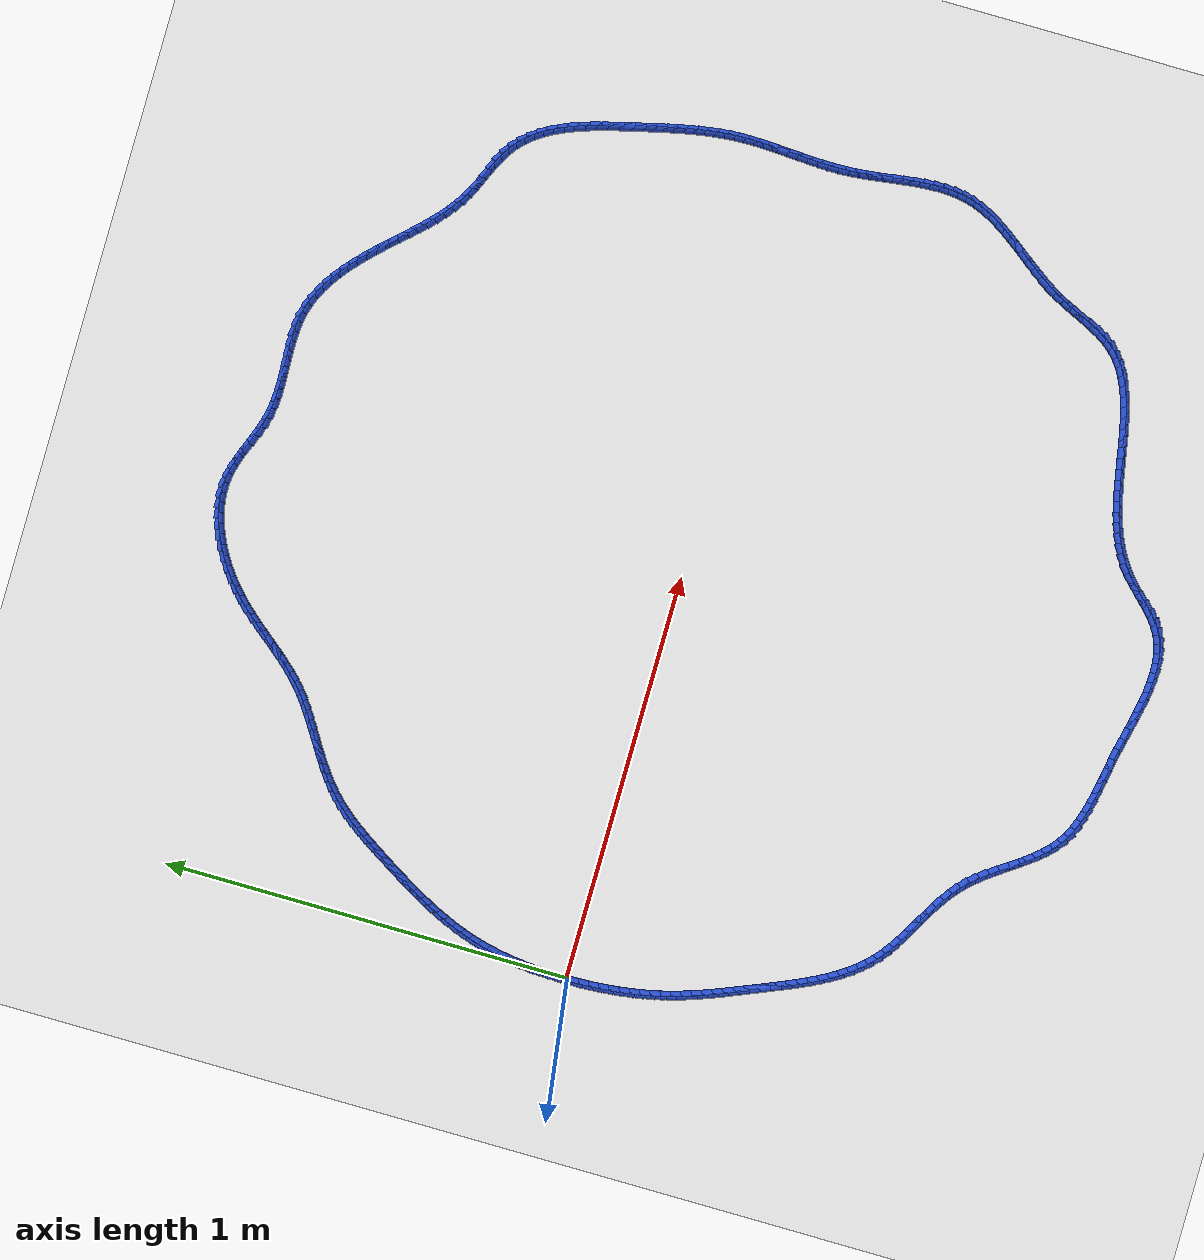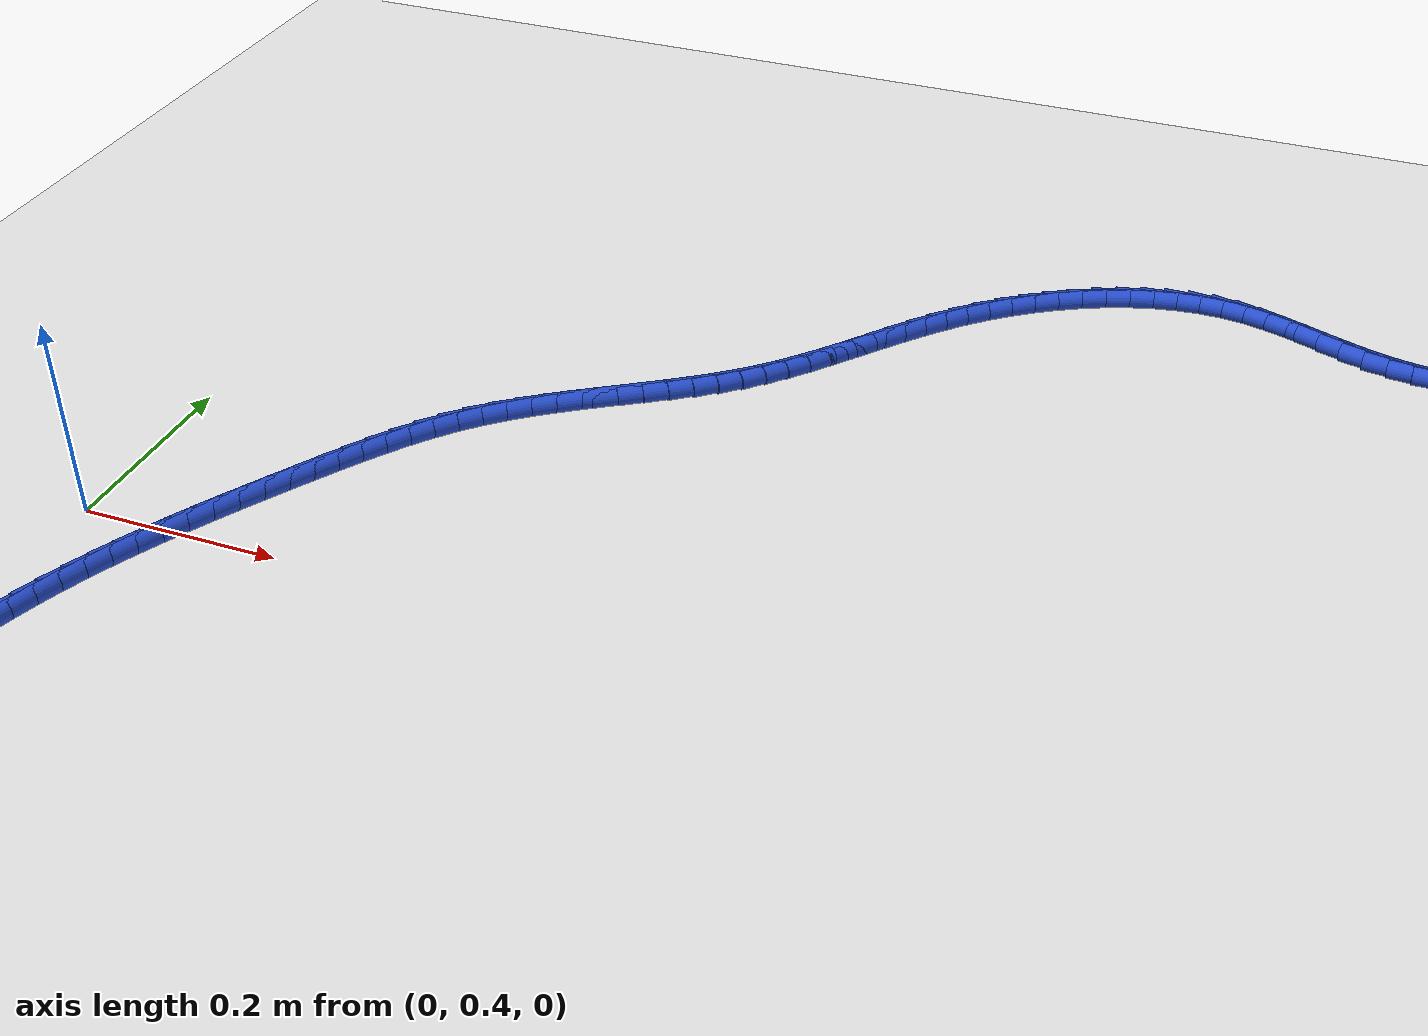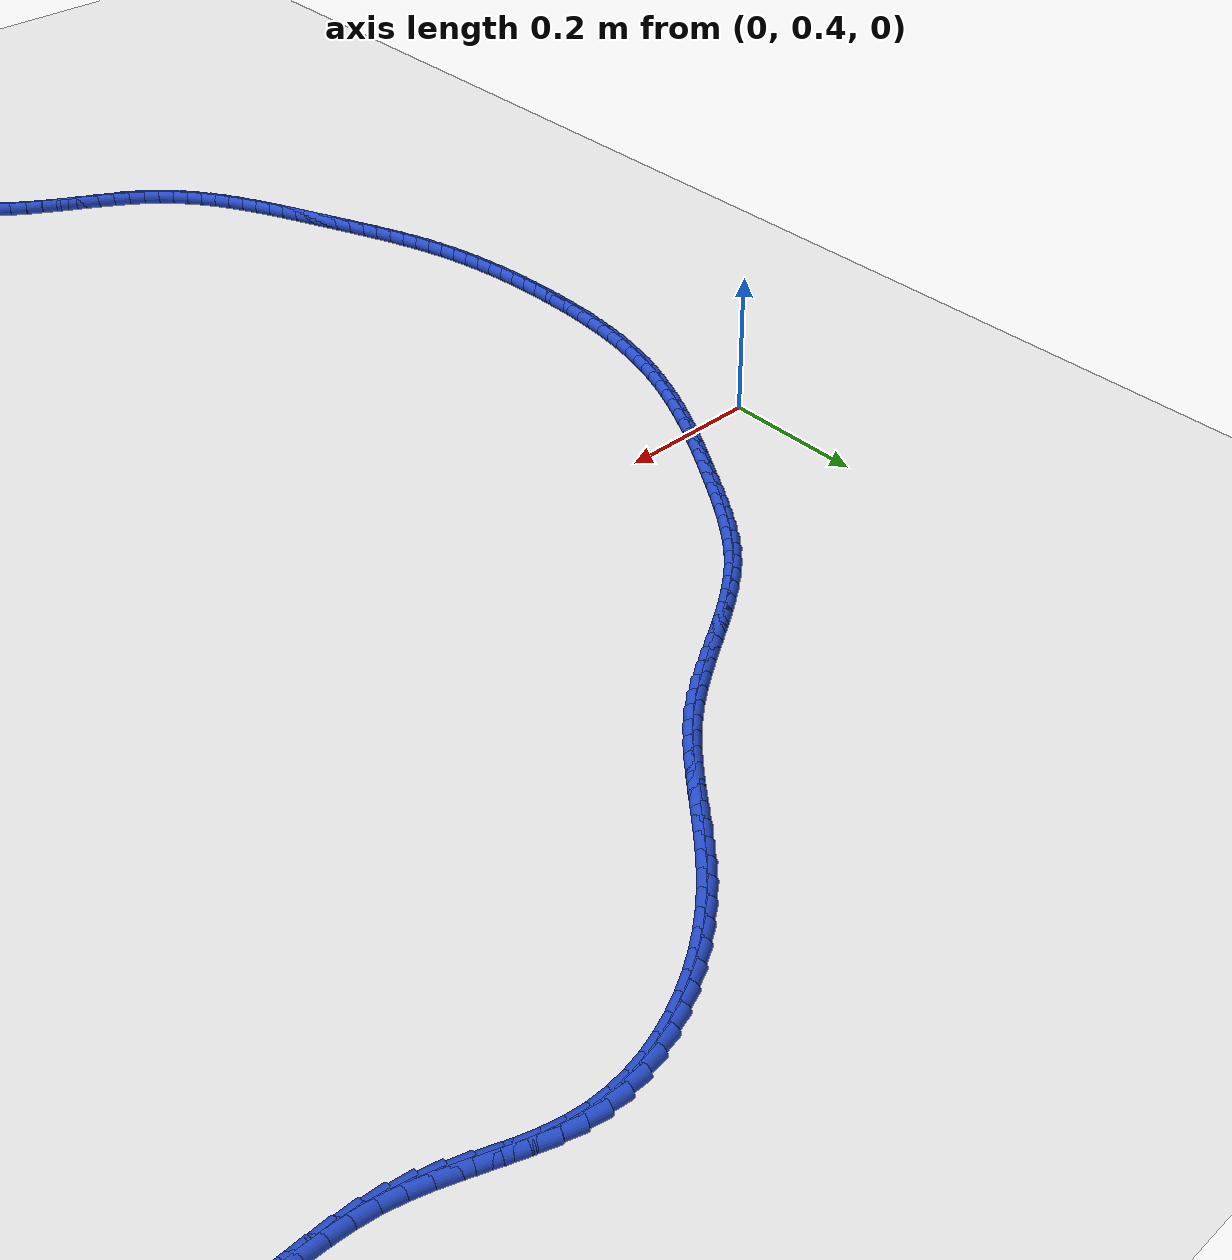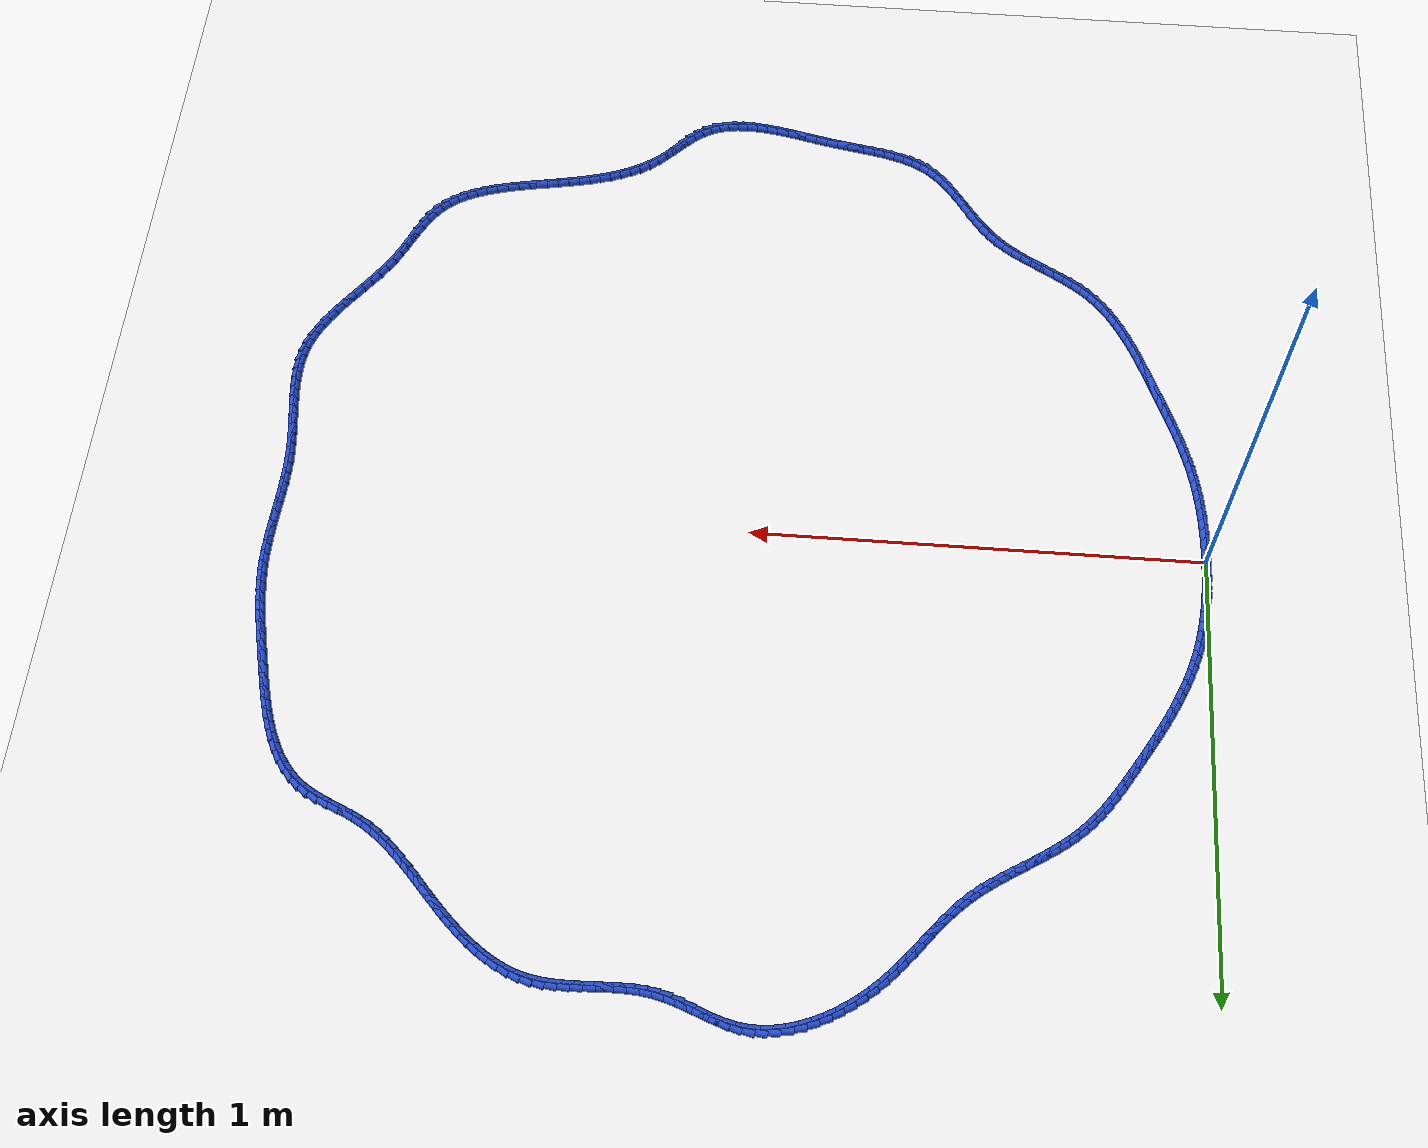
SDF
<sdf version="1.6">
 <world name="default">
  <light name="sun" type="directional">
   <pose>0 0 10 0 -0 0</pose>
   <diffuse>0.8 0.8 0.8 1</diffuse>
   <specular>0.2 0.2 0.2 1</specular>
   <attenuation>
    <range>1000</range>
    <constant>0.9</constant>
    <linear>0.01</linear>
    <quadratic>0.001</quadratic>
   </attenuation>
   <direction>-0.5 0.1 -0.9</direction>
  </light>
  <model name="ground_plane">
   <static>1</static>
   <link name="link">
    <collision name="collision">
     <geometry><plane><normal>0 0 1</normal><size>100 100</size></plane></geometry>
     <surface><friction><ode><mu>100</mu><mu2>50</mu2></ode></friction></surface>
    </collision>
    <visual name="visual">
     <cast_shadows>0</cast_shadows>
     <geometry><plane><normal>0 0 1</normal><size>100 100</size></plane></geometry>
     <material>
      <script><uri>file://media/materials/scripts/gazebo.material</uri><name>Gazebo/WhiteGlow</name></script>
     </material>
    </visual>
   </link>
  </model>
  <gravity>0 0 -9.8</gravity>
  <magnetic_field>6e-06 2.3e-05 -4.2e-05</magnetic_field>
  <atmosphere type="adiabatic"/>
  <physics name="default_physics" default="0" type="ode">
   <max_step_size>0.001</max_step_size>
   <real_time_factor>1</real_time_factor>
   <real_time_update_rate>1000</real_time_update_rate>
  </physics>
  <scene><ambient>0.4 0.4 0.4 1</ambient><background>0.7 0.7 0.7 1</background><shadows>1</shadows></scene>
  <spherical_coordinates>
   <surface_model>EARTH_WGS84</surface_model>
   <latitude_deg>0</latitude_deg>
   <longitude_deg>0</longitude_deg>
   <elevation>0</elevation>
   <heading_deg>0</heading_deg>
  </spherical_coordinates>
  <model name="line">
   <link name="link_0">
    <pose>1.3010426069826053e-17 6.938893903907228e-18 0.01 0 1.57 1.5672710276396127</pose>
    <collision name="collision">
     <geometry><cylinder><radius>0.01</radius><length>0.08</length></cylinder></geometry>
    </collision>
    <visual name="visual">
     <material>
      <script><name>Gazebo/Blue</name><uri>file://media/materials/scripts/gazebo.material</uri></script>
     </material>
     <geometry><cylinder><radius>0.01</radius><length>0.08</length></cylinder></geometry>
    </visual>
   </link>
   <link name="link_1">
    <pose>8.916181260796282e-05 0.02529188001371106 0.01 0 1.57 1.5455889791197208</pose>
    <collision name="collision">
     <geometry><cylinder><radius>0.01</radius><length>0.08</length></cylinder></geometry>
    </collision>
    <visual name="visual">
     <material>
      <script><name>Gazebo/Blue</name><uri>file://media/materials/scripts/gazebo.material</uri></script>
     </material>
     <geometry><cylinder><radius>0.01</radius><length>0.08</length></cylinder></geometry>
    </visual>
   </link>
   <link name="link_2">
    <pose>0.0007263019309446944 0.05056249445309953 0.01 0 1.57 1.5216804252709202</pose>
    <collision name="collision">
     <geometry><cylinder><radius>0.01</radius><length>0.08</length></cylinder></geometry>
    </collision>
    <visual name="visual">
     <material>
      <script><name>Gazebo/Blue</name><uri>file://media/materials/scripts/gazebo.material</uri></script>
     </material>
     <geometry><cylinder><radius>0.01</radius><length>0.08</length></cylinder></geometry>
    </visual>
   </link>
   <link name="link_3">
    <pose>0.001965688934207234 0.07577612555371355 0.01 0 1.57 1.4954681000612848</pose>
    <collision name="collision">
     <geometry><cylinder><radius>0.01</radius><length>0.08</length></cylinder></geometry>
    </collision>
    <visual name="visual">
     <material>
      <script><name>Gazebo/Blue</name><uri>file://media/materials/scripts/gazebo.material</uri></script>
     </material>
     <geometry><cylinder><radius>0.01</radius><length>0.08</length></cylinder></geometry>
    </visual>
   </link>
   <link name="link_4">
    <pose>0.0038615914015926065 0.10089705555110126 0.01 0 1.57 1.4668733684894117</pose>
    <collision name="collision">
     <geometry><cylinder><radius>0.01</radius><length>0.08</length></cylinder></geometry>
    </collision>
    <visual name="visual">
     <material>
      <script><name>Gazebo/Blue</name><uri>file://media/materials/scripts/gazebo.material</uri></script>
     </material>
     <geometry><cylinder><radius>0.01</radius><length>0.08</length></cylinder></geometry>
    </visual>
   </link>
   <link name="link_5">
    <pose>0.0064682779122978325 0.12588956668081078 0.01 0 1.57 1.4358201870816005</pose>
    <collision name="collision">
     <geometry><cylinder><radius>0.01</radius><length>0.08</length></cylinder></geometry>
    </collision>
    <visual name="visual">
     <material>
      <script><name>Gazebo/Blue</name><uri>file://media/materials/scripts/gazebo.material</uri></script>
     </material>
     <geometry><cylinder><radius>0.01</radius><length>0.08</length></cylinder></geometry>
    </visual>
   </link>
   <link name="link_6">
    <pose>0.009840017045519945 0.15071794117839038 0.01 0 1.57 1.4022399600396902</pose>
    <collision name="collision">
     <geometry><cylinder><radius>0.01</radius><length>0.08</length></cylinder></geometry>
    </collision>
    <visual name="visual">
     <material>
      <script><name>Gazebo/Blue</name><uri>file://media/materials/scripts/gazebo.material</uri></script>
     </material>
     <geometry><cylinder><radius>0.01</radius><length>0.08</length></cylinder></geometry>
    </visual>
   </link>
   <link name="link_7">
    <pose>0.014031077380455963 0.17534646127938808 0.01 0 1.57 1.366077375018082</pose>
    <collision name="collision">
     <geometry><cylinder><radius>0.01</radius><length>0.08</length></cylinder></geometry>
    </collision>
    <visual name="visual">
     <material>
      <script><name>Gazebo/Blue</name><uri>file://media/materials/scripts/gazebo.material</uri></script>
     </material>
     <geometry><cylinder><radius>0.01</radius><length>0.08</length></cylinder></geometry>
    </visual>
   </link>
   <link name="link_8">
    <pose>0.01909572749630291 0.19973940921935207 0.01 0 1.57 1.3272972233055258</pose>
    <collision name="collision">
     <geometry><cylinder><radius>0.01</radius><length>0.08</length></cylinder></geometry>
    </collision>
    <visual name="visual">
     <material>
      <script><name>Gazebo/Blue</name><uri>file://media/materials/scripts/gazebo.material</uri></script>
     </material>
     <geometry><cylinder><radius>0.01</radius><length>0.08</length></cylinder></geometry>
    </visual>
   </link>
   <link name="link_9">
    <pose>0.025088235972257802 0.22386106723383054 0.01 0 1.57 1.2862354107738991</pose>
    <collision name="collision">
     <geometry><cylinder><radius>0.01</radius><length>0.08</length></cylinder></geometry>
    </collision>
    <visual name="visual">
     <material>
      <script><name>Gazebo/Blue</name><uri>file://media/materials/scripts/gazebo.material</uri></script>
     </material>
     <geometry><cylinder><radius>0.01</radius><length>0.08</length></cylinder></geometry>
    </visual>
   </link>
   <link name="link_10">
    <pose>0.03205500438986558 0.24767916917425398 0.01 0 1.57 1.2462751749539023</pose>
    <collision name="collision">
     <geometry><cylinder><radius>0.01</radius><length>0.08</length></cylinder></geometry>
    </collision>
    <visual name="visual">
     <material>
      <script><name>Gazebo/Blue</name><uri>file://media/materials/scripts/gazebo.material</uri></script>
     </material>
     <geometry><cylinder><radius>0.01</radius><length>0.08</length></cylinder></geometry>
    </visual>
   </link>
   <link name="link_11">
    <pose>0.03996605973799737 0.27119495795977494 0.01 0 1.57 1.2093929623774209</pose>
    <collision name="collision">
     <geometry><cylinder><radius>0.01</radius><length>0.08</length></cylinder></geometry>
    </collision>
    <visual name="visual">
     <material>
      <script><name>Gazebo/Blue</name><uri>file://media/materials/scripts/gazebo.material</uri></script>
     </material>
     <geometry><cylinder><radius>0.01</radius><length>0.08</length></cylinder></geometry>
    </visual>
   </link>
   <link name="link_12">
    <pose>0.04874848270225565 0.2944285190399502 0.01 0 1.57 1.175675845342847</pose>
    <collision name="collision">
     <geometry><cylinder><radius>0.01</radius><length>0.08</length></cylinder></geometry>
    </collision>
    <visual name="visual">
     <material>
      <script><name>Gazebo/Blue</name><uri>file://media/materials/scripts/gazebo.material</uri></script>
     </material>
     <geometry><cylinder><radius>0.01</radius><length>0.08</length></cylinder></geometry>
    </visual>
   </link>
   <link name="link_13">
    <pose>0.05832887542737812 0.31740014782235704 0.01 0 1.57 1.1451482526437538</pose>
    <collision name="collision">
     <geometry><cylinder><radius>0.01</radius><length>0.08</length></cylinder></geometry>
    </collision>
    <visual name="visual">
     <material>
      <script><name>Gazebo/Blue</name><uri>file://media/materials/scripts/gazebo.material</uri></script>
     </material>
     <geometry><cylinder><radius>0.01</radius><length>0.08</length></cylinder></geometry>
    </visual>
   </link>
   <link name="link_14">
    <pose>0.0686338400581025 0.3401301397145725 0.01 0 1.57 1.1178028867641747</pose>
    <collision name="collision">
     <geometry><cylinder><radius>0.01</radius><length>0.08</length></cylinder></geometry>
    </collision>
    <visual name="visual">
     <material>
      <script><name>Gazebo/Blue</name><uri>file://media/materials/scripts/gazebo.material</uri></script>
     </material>
     <geometry><cylinder><radius>0.01</radius><length>0.08</length></cylinder></geometry>
    </visual>
   </link>
   <link name="link_15">
    <pose>0.07958997873916643 0.36263879012417366 0.01 0 1.57 1.0936101454857605</pose>
    <collision name="collision">
     <geometry><cylinder><radius>0.01</radius><length>0.08</length></cylinder></geometry>
    </collision>
    <visual name="visual">
     <material>
      <script><name>Gazebo/Blue</name><uri>file://media/materials/scripts/gazebo.material</uri></script>
     </material>
     <geometry><cylinder><radius>0.01</radius><length>0.08</length></cylinder></geometry>
    </visual>
   </link>
   <link name="link_16">
    <pose>0.09112389361530761 0.38494639445873746 0.01 0 1.57 1.0725265043926129</pose>
    <collision name="collision">
     <geometry><cylinder><radius>0.01</radius><length>0.08</length></cylinder></geometry>
    </collision>
    <visual name="visual">
     <material>
      <script><name>Gazebo/Blue</name><uri>file://media/materials/scripts/gazebo.material</uri></script>
     </material>
     <geometry><cylinder><radius>0.01</radius><length>0.08</length></cylinder></geometry>
    </visual>
   </link>
   <link name="link_17">
    <pose>0.10316218683126376 0.4070732481258412 0.01 0 1.57 1.0545016699259593</pose>
    <collision name="collision">
     <geometry><cylinder><radius>0.01</radius><length>0.08</length></cylinder></geometry>
    </collision>
    <visual name="visual">
     <material>
      <script><name>Gazebo/Blue</name><uri>file://media/materials/scripts/gazebo.material</uri></script>
     </material>
     <geometry><cylinder><radius>0.01</radius><length>0.08</length></cylinder></geometry>
    </visual>
   </link>
   <link name="link_18">
    <pose>0.11563146053177244 0.4290396465330616 0.01 0 1.57 1.039484480454887</pose>
    <collision name="collision">
     <geometry><cylinder><radius>0.01</radius><length>0.08</length></cylinder></geometry>
    </collision>
    <visual name="visual">
     <material>
      <script><name>Gazebo/Blue</name><uri>file://media/materials/scripts/gazebo.material</uri></script>
     </material>
     <geometry><cylinder><radius>0.01</radius><length>0.08</length></cylinder></geometry>
    </visual>
   </link>
   <link name="link_19">
    <pose>0.12845831686157147 0.450865885087976 0.01 0 1.57 1.027427636774409</pose>
    <collision name="collision">
     <geometry><cylinder><radius>0.01</radius><length>0.08</length></cylinder></geometry>
    </collision>
    <visual name="visual">
     <material>
      <script><name>Gazebo/Blue</name><uri>file://media/materials/scripts/gazebo.material</uri></script>
     </material>
     <geometry><cylinder><radius>0.01</radius><length>0.08</length></cylinder></geometry>
    </visual>
   </link>
   <link name="link_20">
    <pose>0.14156935796539846 0.47257225919816126 0.01 0 1.57 1.0182913958750723</pose>
    <collision name="collision">
     <geometry><cylinder><radius>0.01</radius><length>0.08</length></cylinder></geometry>
    </collision>
    <visual name="visual">
     <material>
      <script><name>Gazebo/Blue</name><uri>file://media/materials/scripts/gazebo.material</uri></script>
     </material>
     <geometry><cylinder><radius>0.01</radius><length>0.08</length></cylinder></geometry>
    </visual>
   </link>
   <link name="link_21">
    <pose>0.15489118598799115 0.4941790642711946 0.01 0 1.57 1.0118851558748796</pose>
    <collision name="collision">
     <geometry><cylinder><radius>0.01</radius><length>0.08</length></cylinder></geometry>
    </collision>
    <visual name="visual">
     <material>
      <script><name>Gazebo/Blue</name><uri>file://media/materials/scripts/gazebo.material</uri></script>
     </material>
     <geometry><cylinder><radius>0.01</radius><length>0.08</length></cylinder></geometry>
    </visual>
   </link>
   <link name="link_22">
    <pose>0.16835364390508534 0.515704058292417 0.01 0 1.57 1.0033464394424578</pose>
    <collision name="collision">
     <geometry><cylinder><radius>0.01</radius><length>0.08</length></cylinder></geometry>
    </collision>
    <visual name="visual">
     <material>
      <script><name>Gazebo/Blue</name><uri>file://media/materials/scripts/gazebo.material</uri></script>
     </material>
     <geometry><cylinder><radius>0.01</radius><length>0.08</length></cylinder></geometry>
    </visual>
   </link>
   <link name="link_23">
    <pose>0.18198381784760354 0.5370888623105591 0.01 0 1.57 0.9870378730563506</pose>
    <collision name="collision">
     <geometry><cylinder><radius>0.01</radius><length>0.08</length></cylinder></geometry>
    </collision>
    <visual name="visual">
     <material>
      <script><name>Gazebo/Blue</name><uri>file://media/materials/scripts/gazebo.material</uri></script>
     </material>
     <geometry><cylinder><radius>0.01</radius><length>0.08</length></cylinder></geometry>
    </visual>
   </link>
   <link name="link_24">
    <pose>0.195920623145529 0.5581875402334536 0.01 0 1.57 0.9625015057356455</pose>
    <collision name="collision">
     <geometry><cylinder><radius>0.01</radius><length>0.08</length></cylinder></geometry>
    </collision>
    <visual name="visual">
     <material>
      <script><name>Gazebo/Blue</name><uri>file://media/materials/scripts/gazebo.material</uri></script>
     </material>
     <geometry><cylinder><radius>0.01</radius><length>0.08</length></cylinder></geometry>
    </visual>
   </link>
   <link name="link_25">
    <pose>0.21030915104220657 0.5788493205116382 0.01 0 1.57 0.9295384138976541</pose>
    <collision name="collision">
     <geometry><cylinder><radius>0.01</radius><length>0.08</length></cylinder></geometry>
    </collision>
    <visual name="visual">
     <material>
      <script><name>Gazebo/Blue</name><uri>file://media/materials/scripts/gazebo.material</uri></script>
     </material>
     <geometry><cylinder><radius>0.01</radius><length>0.08</length></cylinder></geometry>
    </visual>
   </link>
   <link name="link_26">
    <pose>0.22529449278098138 0.5989234315956501 0.01 0 1.57 0.8879499518997398</pose>
    <collision name="collision">
     <geometry><cylinder><radius>0.01</radius><length>0.08</length></cylinder></geometry>
    </collision>
    <visual name="visual">
     <material>
      <script><name>Gazebo/Blue</name><uri>file://media/materials/scripts/gazebo.material</uri></script>
     </material>
     <geometry><cylinder><radius>0.01</radius><length>0.08</length></cylinder></geometry>
    </visual>
   </link>
   <link name="link_27">
    <pose>0.24102173960519843 0.6182591019360267 0.01 0 1.57 0.8376090340198942</pose>
    <collision name="collision">
     <geometry><cylinder><radius>0.01</radius><length>0.08</length></cylinder></geometry>
    </collision>
    <visual name="visual">
     <material>
      <script><name>Gazebo/Blue</name><uri>file://media/materials/scripts/gazebo.material</uri></script>
     </material>
     <geometry><cylinder><radius>0.01</radius><length>0.08</length></cylinder></geometry>
    </visual>
   </link>
   <link name="link_28">
    <pose>0.25763598275820276 0.6367055599833061 0.01 0 1.57 0.7785646178513194</pose>
    <collision name="collision">
     <geometry><cylinder><radius>0.01</radius><length>0.08</length></cylinder></geometry>
    </collision>
    <visual name="visual">
     <material>
      <script><name>Gazebo/Blue</name><uri>file://media/materials/scripts/gazebo.material</uri></script>
     </material>
     <geometry><cylinder><radius>0.01</radius><length>0.08</length></cylinder></geometry>
    </visual>
   </link>
   <link name="link_29">
    <pose>0.27528215511007487 0.6541121936600438 0.01 0 1.57 0.7159772517470793</pose>
    <collision name="collision">
     <geometry><cylinder><radius>0.01</radius><length>0.08</length></cylinder></geometry>
    </collision>
    <visual name="visual">
     <material>
      <script><name>Gazebo/Blue</name><uri>file://media/materials/scripts/gazebo.material</uri></script>
     </material>
     <geometry><cylinder><radius>0.01</radius><length>0.08</length></cylinder></geometry>
    </visual>
   </link>
   <link name="link_30">
    <pose>0.29402027123768876 0.6704138983236908 0.01 0 1.57 0.6630237667221597</pose>
    <collision name="collision">
     <geometry><cylinder><radius>0.01</radius><length>0.08</length></cylinder></geometry>
    </collision>
    <visual name="visual">
     <material>
      <script><name>Gazebo/Blue</name><uri>file://media/materials/scripts/gazebo.material</uri></script>
     </material>
     <geometry><cylinder><radius>0.01</radius><length>0.08</length></cylinder></geometry>
    </visual>
   </link>
   <link name="link_31">
    <pose>0.31368566309640433 0.6857718107445425 0.01 0 1.57 0.6217759222436743</pose>
    <collision name="collision">
     <geometry><cylinder><radius>0.01</radius><length>0.08</length></cylinder></geometry>
    </collision>
    <visual name="visual">
     <material>
      <script><name>Gazebo/Blue</name><uri>file://media/materials/scripts/gazebo.material</uri></script>
     </material>
     <geometry><cylinder><radius>0.01</radius><length>0.08</length></cylinder></geometry>
    </visual>
   </link>
   <link name="link_32">
    <pose>0.33407692760737157 0.7003840575855007 0.01 0 1.57 0.5919932194578194</pose>
    <collision name="collision">
     <geometry><cylinder><radius>0.01</radius><length>0.08</length></cylinder></geometry>
    </collision>
    <visual name="visual">
     <material>
      <script><name>Gazebo/Blue</name><uri>file://media/materials/scripts/gazebo.material</uri></script>
     </material>
     <geometry><cylinder><radius>0.01</radius><length>0.08</length></cylinder></geometry>
    </visual>
   </link>
   <link name="link_33">
    <pose>0.3549926616917402 0.714448765509468 0.01 0 1.57 0.5733930223101903</pose>
    <collision name="collision">
     <geometry><cylinder><radius>0.01</radius><length>0.08</length></cylinder></geometry>
    </collision>
    <visual name="visual">
     <material>
      <script><name>Gazebo/Blue</name><uri>file://media/materials/scripts/gazebo.material</uri></script>
     </material>
     <geometry><cylinder><radius>0.01</radius><length>0.08</length></cylinder></geometry>
    </visual>
   </link>
   <link name="link_34">
    <pose>0.37623146227066 0.7281640611793464 0.01 0 1.57 0.565761881200285</pose>
    <collision name="collision">
     <geometry><cylinder><radius>0.01</radius><length>0.08</length></cylinder></geometry>
    </collision>
    <visual name="visual">
     <material>
      <script><name>Gazebo/Blue</name><uri>file://media/materials/scripts/gazebo.material</uri></script>
     </material>
     <geometry><cylinder><radius>0.01</radius><length>0.08</length></cylinder></geometry>
    </visual>
   </link>
   <link name="link_35">
    <pose>0.3975919262652808 0.741728071258038 0.01 0 1.57 0.5690193621223153</pose>
    <collision name="collision">
     <geometry><cylinder><radius>0.01</radius><length>0.08</length></cylinder></geometry>
    </collision>
    <visual name="visual">
     <material>
      <script><name>Gazebo/Blue</name><uri>file://media/materials/scripts/gazebo.material</uri></script>
     </material>
     <geometry><cylinder><radius>0.01</radius><length>0.08</length></cylinder></geometry>
    </visual>
   </link>
   <link name="link_36">
    <pose>0.4188726505967526 0.7553389224084452 0.01 0 1.57 0.5832434651503329</pose>
    <collision name="collision">
     <geometry><cylinder><radius>0.01</radius><length>0.08</length></cylinder></geometry>
    </collision>
    <visual name="visual">
     <material>
      <script><name>Gazebo/Blue</name><uri>file://media/materials/scripts/gazebo.material</uri></script>
     </material>
     <geometry><cylinder><radius>0.01</radius><length>0.08</length></cylinder></geometry>
    </visual>
   </link>
   <link name="link_37">
    <pose>0.4398722321862252 0.7691947412934705 0.01 0 1.57 0.608661786370115</pose>
    <collision name="collision">
     <geometry><cylinder><radius>0.01</radius><length>0.08</length></cylinder></geometry>
    </collision>
    <visual name="visual">
     <material>
      <script><name>Gazebo/Blue</name><uri>file://media/materials/scripts/gazebo.material</uri></script>
     </material>
     <geometry><cylinder><radius>0.01</radius><length>0.08</length></cylinder></geometry>
    </visual>
   </link>
   <link name="link_38">
    <pose>0.46038926795484836 0.7834936545760157 0.01 0 1.57 0.6456055839524886</pose>
    <collision name="collision">
     <geometry><cylinder><radius>0.01</radius><length>0.08</length></cylinder></geometry>
    </collision>
    <visual name="visual">
     <material>
      <script><name>Gazebo/Blue</name><uri>file://media/materials/scripts/gazebo.material</uri></script>
     </material>
     <geometry><cylinder><radius>0.01</radius><length>0.08</length></cylinder></geometry>
    </visual>
   </link>
   <link name="link_39">
    <pose>0.48022235482377185 0.7984337889189832 0.01 0 1.57 0.6944174701596125</pose>
    <collision name="collision">
     <geometry><cylinder><radius>0.01</radius><length>0.08</length></cylinder></geometry>
    </collision>
    <visual name="visual">
     <material>
      <script><name>Gazebo/Blue</name><uri>file://media/materials/scripts/gazebo.material</uri></script>
     </material>
     <geometry><cylinder><radius>0.01</radius><length>0.08</length></cylinder></geometry>
    </visual>
   </link>
   <link name="link_40">
    <pose>0.49917008971414545 0.8142132709852751 0.01 0 1.57 0.7520376965207981</pose>
    <collision name="collision">
     <geometry><cylinder><radius>0.01</radius><length>0.08</length></cylinder></geometry>
    </collision>
    <visual name="visual">
     <material>
      <script><name>Gazebo/Blue</name><uri>file://media/materials/scripts/gazebo.material</uri></script>
     </material>
     <geometry><cylinder><radius>0.01</radius><length>0.08</length></cylinder></geometry>
    </visual>
   </link>
   <link name="link_41">
    <pose>0.5170914558307381 0.8309770935633699 0.01 0 1.57 0.802877534121172</pose>
    <collision name="collision">
     <geometry><cylinder><radius>0.01</radius><length>0.08</length></cylinder></geometry>
    </collision>
    <visual name="visual">
     <material>
      <script><name>Gazebo/Blue</name><uri>file://media/materials/scripts/gazebo.material</uri></script>
     </material>
     <geometry><cylinder><radius>0.01</radius><length>0.08</length></cylinder></geometry>
    </visual>
   </link>
   <link name="link_42">
    <pose>0.5341289133847011 0.8486208181014416 0.01 0 1.57 0.8419807267060411</pose>
    <collision name="collision">
     <geometry><cylinder><radius>0.01</radius><length>0.08</length></cylinder></geometry>
    </collision>
    <visual name="visual">
     <material>
      <script><name>Gazebo/Blue</name><uri>file://media/materials/scripts/gazebo.material</uri></script>
     </material>
     <geometry><cylinder><radius>0.01</radius><length>0.08</length></cylinder></geometry>
    </visual>
   </link>
   <link name="link_43">
    <pose>0.5505080331699483 0.8669668770686445 0.01 0 1.57 0.8691960006259388</pose>
    <collision name="collision">
     <geometry><cylinder><radius>0.01</radius><length>0.08</length></cylinder></geometry>
    </collision>
    <visual name="visual">
     <material>
      <script><name>Gazebo/Blue</name><uri>file://media/materials/scripts/gazebo.material</uri></script>
     </material>
     <geometry><cylinder><radius>0.01</radius><length>0.08</length></cylinder></geometry>
    </visual>
   </link>
   <link name="link_44">
    <pose>0.5664543967383258 0.8858376934682319 0.01 0 1.57 0.8845878296593362</pose>
    <collision name="collision">
     <geometry><cylinder><radius>0.01</radius><length>0.08</length></cylinder></geometry>
    </collision>
    <visual name="visual">
     <material>
      <script><name>Gazebo/Blue</name><uri>file://media/materials/scripts/gazebo.material</uri></script>
     </material>
     <geometry><cylinder><radius>0.01</radius><length>0.08</length></cylinder></geometry>
    </visual>
   </link>
   <link name="link_45">
    <pose>0.5821935856416789 0.9050556903034573 0.01 0 1.57 0.8883191486361897</pose>
    <collision name="collision">
     <geometry><cylinder><radius>0.01</radius><length>0.08</length></cylinder></geometry>
    </collision>
    <visual name="visual">
     <material>
      <script><name>Gazebo/Blue</name><uri>file://media/materials/scripts/gazebo.material</uri></script>
     </material>
     <geometry><cylinder><radius>0.01</radius><length>0.08</length></cylinder></geometry>
    </visual>
   </link>
   <link name="link_46">
    <pose>0.5979511814318536 0.924443290577574 0.01 0 1.57 0.8805852383725722</pose>
    <collision name="collision">
     <geometry><cylinder><radius>0.01</radius><length>0.08</length></cylinder></geometry>
    </collision>
    <visual name="visual">
     <material>
      <script><name>Gazebo/Blue</name><uri>file://media/materials/scripts/gazebo.material</uri></script>
     </material>
     <geometry><cylinder><radius>0.01</radius><length>0.08</length></cylinder></geometry>
    </visual>
   </link>
   <link name="link_47">
    <pose>0.613952765660696 0.9438229172938362 0.01 0 1.57 0.8615970234336856</pose>
    <collision name="collision">
     <geometry><cylinder><radius>0.01</radius><length>0.08</length></cylinder></geometry>
    </collision>
    <visual name="visual">
     <material>
      <script><name>Gazebo/Blue</name><uri>file://media/materials/scripts/gazebo.material</uri></script>
     </material>
     <geometry><cylinder><radius>0.01</radius><length>0.08</length></cylinder></geometry>
    </visual>
   </link>
   <link name="link_48">
    <pose>0.6304239198800514 0.9630169934554969 0.01 0 1.57 0.8316088480989581</pose>
    <collision name="collision">
     <geometry><cylinder><radius>0.01</radius><length>0.08</length></cylinder></geometry>
    </collision>
    <visual name="visual">
     <material>
      <script><name>Gazebo/Blue</name><uri>file://media/materials/scripts/gazebo.material</uri></script>
     </material>
     <geometry><cylinder><radius>0.01</radius><length>0.08</length></cylinder></geometry>
    </visual>
   </link>
   <link name="link_49">
    <pose>0.6475902256417657 0.9818479420658095 0.01 0 1.57 0.7909841521365294</pose>
    <collision name="collision">
     <geometry><cylinder><radius>0.01</radius><length>0.08</length></cylinder></geometry>
    </collision>
    <visual name="visual">
     <material>
      <script><name>Gazebo/Blue</name><uri>file://media/materials/scripts/gazebo.material</uri></script>
     </material>
     <geometry><cylinder><radius>0.01</radius><length>0.08</length></cylinder></geometry>
    </visual>
   </link>
   <link name="link_50">
    <pose>0.6656772644976847 1.0001381861280276 0.01 0 1.57 0.7403847587094323</pose>
    <collision name="collision">
     <geometry><cylinder><radius>0.01</radius><length>0.08</length></cylinder></geometry>
    </collision>
    <visual name="visual">
     <material>
      <script><name>Gazebo/Blue</name><uri>file://media/materials/scripts/gazebo.material</uri></script>
     </material>
     <geometry><cylinder><radius>0.01</radius><length>0.08</length></cylinder></geometry>
    </visual>
   </link>
   <link name="link_51">
    <pose>0.6849066985267032 1.0177099530618334 0.01 0 1.57 0.684148161096767</pose>
    <collision name="collision">
     <geometry><cylinder><radius>0.01</radius><length>0.08</length></cylinder></geometry>
    </collision>
    <visual name="visual">
     <material>
      <script><name>Gazebo/Blue</name><uri>file://media/materials/scripts/gazebo.material</uri></script>
     </material>
     <geometry><cylinder><radius>0.01</radius><length>0.08</length></cylinder></geometry>
    </visual>
   </link>
   <link name="link_52">
    <pose>0.7053442329618272 1.034377687965857 0.01 0 1.57 0.6265645961025219</pose>
    <collision name="collision">
     <geometry><cylinder><radius>0.01</radius><length>0.08</length></cylinder></geometry>
    </collision>
    <visual name="visual">
     <material>
      <script><name>Gazebo/Blue</name><uri>file://media/materials/scripts/gazebo.material</uri></script>
     </material>
     <geometry><cylinder><radius>0.01</radius><length>0.08</length></cylinder></geometry>
    </visual>
   </link>
   <link name="link_53">
    <pose>0.7268508794668234 1.0499456216319174 0.01 0 1.57 0.5668106795794612</pose>
    <collision name="collision">
     <geometry><cylinder><radius>0.01</radius><length>0.08</length></cylinder></geometry>
    </collision>
    <visual name="visual">
     <material>
      <script><name>Gazebo/Blue</name><uri>file://media/materials/scripts/gazebo.material</uri></script>
     </material>
     <geometry><cylinder><radius>0.01</radius><length>0.08</length></cylinder></geometry>
    </visual>
   </link>
   <link name="link_54">
    <pose>0.7492737563738415 1.0642172915679537 0.01 0 1.57 0.5037209179061823</pose>
    <collision name="collision">
     <geometry><cylinder><radius>0.01</radius><length>0.08</length></cylinder></geometry>
    </collision>
    <visual name="visual">
     <material>
      <script><name>Gazebo/Blue</name><uri>file://media/materials/scripts/gazebo.material</uri></script>
     </material>
     <geometry><cylinder><radius>0.01</radius><length>0.08</length></cylinder></geometry>
    </visual>
   </link>
   <link name="link_55">
    <pose>0.7724599820150326 1.0769962352819054 0.01 0 1.57 0.4360967059583024</pose>
    <collision name="collision">
     <geometry><cylinder><radius>0.01</radius><length>0.08</length></cylinder></geometry>
    </collision>
    <visual name="visual">
     <material>
      <script><name>Gazebo/Blue</name><uri>file://media/materials/scripts/gazebo.material</uri></script>
     </material>
     <geometry><cylinder><radius>0.01</radius><length>0.08</length></cylinder></geometry>
    </visual>
   </link>
   <link name="link_56">
    <pose>0.7962566747225474 1.088085990281712 0.01 0 1.57 0.3626958006954847</pose>
    <collision name="collision">
     <geometry><cylinder><radius>0.01</radius><length>0.08</length></cylinder></geometry>
    </collision>
    <visual name="visual">
     <material>
      <script><name>Gazebo/Blue</name><uri>file://media/materials/scripts/gazebo.material</uri></script>
     </material>
     <geometry><cylinder><radius>0.01</radius><length>0.08</length></cylinder></geometry>
    </visual>
   </link>
   <link name="link_57">
    <pose>0.8205109528285361 1.0972900940753127 0.01 0 1.57 0.2822531162521812</pose>
    <collision name="collision">
     <geometry><cylinder><radius>0.01</radius><length>0.08</length></cylinder></geometry>
    </collision>
    <visual name="visual">
     <material>
      <script><name>Gazebo/Blue</name><uri>file://media/materials/scripts/gazebo.material</uri></script>
     </material>
     <geometry><cylinder><radius>0.01</radius><length>0.08</length></cylinder></geometry>
    </visual>
   </link>
   <link name="link_58">
    <pose>0.8450699346651498 1.104412084170648 0.01 0 1.57 0.19355021864870442</pose>
    <collision name="collision">
     <geometry><cylinder><radius>0.01</radius><length>0.08</length></cylinder></geometry>
    </collision>
    <visual name="visual">
     <material>
      <script><name>Gazebo/Blue</name><uri>file://media/materials/scripts/gazebo.material</uri></script>
     </material>
     <geometry><cylinder><radius>0.01</radius><length>0.08</length></cylinder></geometry>
    </visual>
   </link>
   <link name="link_59">
    <pose>0.8697807385645391 1.1092554980756564 0.01 0 1.57 0.09555591956888013</pose>
    <collision name="collision">
     <geometry><cylinder><radius>0.01</radius><length>0.08</length></cylinder></geometry>
    </collision>
    <visual name="visual">
     <material>
      <script><name>Gazebo/Blue</name><uri>file://media/materials/scripts/gazebo.material</uri></script>
     </material>
     <geometry><cylinder><radius>0.01</radius><length>0.08</length></cylinder></geometry>
    </visual>
   </link>
   <link name="link_60">
    <pose>0.8944904828588546 1.111623873298278 0.01 0 1.57 -0.012343744402836077</pose>
    <collision name="collision">
     <geometry><cylinder><radius>0.01</radius><length>0.08</length></cylinder></geometry>
    </collision>
    <visual name="visual">
     <material>
      <script><name>Gazebo/Blue</name><uri>file://media/materials/scripts/gazebo.material</uri></script>
     </material>
     <geometry><cylinder><radius>0.01</radius><length>0.08</length></cylinder></geometry>
    </visual>
   </link>
   <link name="link_61">
    <pose>0.9190462858802466 1.1113207473464515 0.01 0 1.57 -0.12947252034225032</pose>
    <collision name="collision">
     <geometry><cylinder><radius>0.01</radius><length>0.08</length></cylinder></geometry>
    </collision>
    <visual name="visual">
     <material>
      <script><name>Gazebo/Blue</name><uri>file://media/materials/scripts/gazebo.material</uri></script>
     </material>
     <geometry><cylinder><radius>0.01</radius><length>0.08</length></cylinder></geometry>
    </visual>
   </link>
   <link name="link_62">
    <pose>0.9432990869372014 1.1081630118040486 0.01 0 1.57 -0.2369191574358031</pose>
    <collision name="collision">
     <geometry><cylinder><radius>0.01</radius><length>0.08</length></cylinder></geometry>
    </collision>
    <visual name="visual">
     <material>
      <script><name>Gazebo/Blue</name><uri>file://media/materials/scripts/gazebo.material</uri></script>
     </material>
     <geometry><cylinder><radius>0.01</radius><length>0.08</length></cylinder></geometry>
    </visual>
   </link>
   <link name="link_63">
    <pose>0.967219907651552 1.102387238511926 0.01 0 1.57 -0.31272852563635484</pose>
    <collision name="collision">
     <geometry><cylinder><radius>0.01</radius><length>0.08</length></cylinder></geometry>
    </collision>
    <visual name="visual">
     <material>
      <script><name>Gazebo/Blue</name><uri>file://media/materials/scripts/gazebo.material</uri></script>
     </material>
     <geometry><cylinder><radius>0.01</radius><length>0.08</length></cylinder></geometry>
    </visual>
   </link>
   <link name="link_64">
    <pose>0.9909210442095936 1.0947237451746465 0.01 0 1.57 -0.3566112879373679</pose>
    <collision name="collision">
     <geometry><cylinder><radius>0.01</radius><length>0.08</length></cylinder></geometry>
    </collision>
    <visual name="visual">
     <material>
      <script><name>Gazebo/Blue</name><uri>file://media/materials/scripts/gazebo.material</uri></script>
     </material>
     <geometry><cylinder><radius>0.01</radius><length>0.08</length></cylinder></geometry>
    </visual>
   </link>
   <link name="link_65">
    <pose>1.014522887352018 1.0859311394636713 0.01 0 1.57 -0.3700236242596915</pose>
    <collision name="collision">
     <geometry><cylinder><radius>0.01</radius><length>0.08</length></cylinder></geometry>
    </collision>
    <visual name="visual">
     <material>
      <script><name>Gazebo/Blue</name><uri>file://media/materials/scripts/gazebo.material</uri></script>
     </material>
     <geometry><cylinder><radius>0.01</radius><length>0.08</length></cylinder></geometry>
    </visual>
   </link>
   <link name="link_66">
    <pose>1.0381458278195175 1.0767680290504607 0.01 0 1.57 -0.35371978099237134</pose>
    <collision name="collision">
     <geometry><cylinder><radius>0.01</radius><length>0.08</length></cylinder></geometry>
    </collision>
    <visual name="visual">
     <material>
      <script><name>Gazebo/Blue</name><uri>file://media/materials/scripts/gazebo.material</uri></script>
     </material>
     <geometry><cylinder><radius>0.01</radius><length>0.08</length></cylinder></geometry>
    </visual>
   </link>
   <link name="link_67">
    <pose>1.061910256352784 1.0679930216064752 0.01 0 1.57 -0.30743141323960294</pose>
    <collision name="collision">
     <geometry><cylinder><radius>0.01</radius><length>0.08</length></cylinder></geometry>
    </collision>
    <visual name="visual">
     <material>
      <script><name>Gazebo/Blue</name><uri>file://media/materials/scripts/gazebo.material</uri></script>
     </material>
     <geometry><cylinder><radius>0.01</radius><length>0.08</length></cylinder></geometry>
    </visual>
   </link>
   <link name="link_68">
    <pose>1.0859365636925102 1.0603647248031756 0.01 0 1.57 -0.2305377430001714</pose>
    <collision name="collision">
     <geometry><cylinder><radius>0.01</radius><length>0.08</length></cylinder></geometry>
    </collision>
    <visual name="visual">
     <material>
      <script><name>Gazebo/Blue</name><uri>file://media/materials/scripts/gazebo.material</uri></script>
     </material>
     <geometry><cylinder><radius>0.01</radius><length>0.08</length></cylinder></geometry>
    </visual>
   </link>
   <link name="link_69">
    <pose>1.1103440872834063 1.0546360188912633 0.01 0 1.57 -0.14038997134857908</pose>
    <collision name="collision">
     <geometry><cylinder><radius>0.01</radius><length>0.08</length></cylinder></geometry>
    </collision>
    <visual name="visual">
     <material>
      <script><name>Gazebo/Blue</name><uri>file://media/materials/scripts/gazebo.material</uri></script>
     </material>
     <geometry><cylinder><radius>0.01</radius><length>0.08</length></cylinder></geometry>
    </visual>
   </link>
   <link name="link_70">
    <pose>1.1351726215416915 1.05112725955043 0.01 0 1.57 -0.06730607816485398</pose>
    <collision name="collision">
     <geometry><cylinder><radius>0.01</radius><length>0.08</length></cylinder></geometry>
    </collision>
    <visual name="visual">
     <material>
      <script><name>Gazebo/Blue</name><uri>file://media/materials/scripts/gazebo.material</uri></script>
     </material>
     <geometry><cylinder><radius>0.01</radius><length>0.08</length></cylinder></geometry>
    </visual>
   </link>
   <link name="link_71">
    <pose>1.1603282205221834 1.0494315735184856 0.01 0 1.57 -0.014153819753878225</pose>
    <collision name="collision">
     <geometry><cylinder><radius>0.01</radius><length>0.08</length></cylinder></geometry>
    </collision>
    <visual name="visual">
     <material>
      <script><name>Gazebo/Blue</name><uri>file://media/materials/scripts/gazebo.material</uri></script>
     </material>
     <geometry><cylinder><radius>0.01</radius><length>0.08</length></cylinder></geometry>
    </visual>
   </link>
   <link name="link_72">
    <pose>1.1857041194488427 1.049072383633088 0.01 0 1.57 0.01964204853696827</pose>
    <collision name="collision">
     <geometry><cylinder><radius>0.01</radius><length>0.08</length></cylinder></geometry>
    </collision>
    <visual name="visual">
     <material>
      <script><name>Gazebo/Blue</name><uri>file://media/materials/scripts/gazebo.material</uri></script>
     </material>
     <geometry><cylinder><radius>0.01</radius><length>0.08</length></cylinder></geometry>
    </visual>
   </link>
   <link name="link_73">
    <pose>1.2111935535456335 1.0495731127318964 0.01 0 1.57 0.03466072221899772</pose>
    <collision name="collision">
     <geometry><cylinder><radius>0.01</radius><length>0.08</length></cylinder></geometry>
    </collision>
    <visual name="visual">
     <material>
      <script><name>Gazebo/Blue</name><uri>file://media/materials/scripts/gazebo.material</uri></script>
     </material>
     <geometry><cylinder><radius>0.01</radius><length>0.08</length></cylinder></geometry>
    </visual>
   </link>
   <link name="link_74">
    <pose>1.2366897580365175 1.050457183652568 0.01 0 1.57 0.03112984585743997</pose>
    <collision name="collision">
     <geometry><cylinder><radius>0.01</radius><length>0.08</length></cylinder></geometry>
    </collision>
    <visual name="visual">
     <material>
      <script><name>Gazebo/Blue</name><uri>file://media/materials/scripts/gazebo.material</uri></script>
     </material>
     <geometry><cylinder><radius>0.01</radius><length>0.08</length></cylinder></geometry>
    </visual>
   </link>
   <link name="link_75">
    <pose>1.2620859681454575 1.051248019232762 0.01 0 1.57 0.008774204957133866</pose>
    <collision name="collision">
     <geometry><cylinder><radius>0.01</radius><length>0.08</length></cylinder></geometry>
    </collision>
    <visual name="visual">
     <material>
      <script><name>Gazebo/Blue</name><uri>file://media/materials/scripts/gazebo.material</uri></script>
     </material>
     <geometry><cylinder><radius>0.01</radius><length>0.08</length></cylinder></geometry>
    </visual>
   </link>
   <link name="link_76">
    <pose>1.2872754190964162 1.0514690423101363 0.01 0 1.57 -0.03316716253108689</pose>
    <collision name="collision">
     <geometry><cylinder><radius>0.01</radius><length>0.08</length></cylinder></geometry>
    </collision>
    <visual name="visual">
     <material>
      <script><name>Gazebo/Blue</name><uri>file://media/materials/scripts/gazebo.material</uri></script>
     </material>
     <geometry><cylinder><radius>0.01</radius><length>0.08</length></cylinder></geometry>
    </visual>
   </link>
   <link name="link_77">
    <pose>1.3121513461133556 1.0506436757223487 0.01 0 1.57 -0.0957306996572514</pose>
    <collision name="collision">
     <geometry><cylinder><radius>0.01</radius><length>0.08</length></cylinder></geometry>
    </collision>
    <visual name="visual">
     <material>
      <script><name>Gazebo/Blue</name><uri>file://media/materials/scripts/gazebo.material</uri></script>
     </material>
     <geometry><cylinder><radius>0.01</radius><length>0.08</length></cylinder></geometry>
    </visual>
   </link>
   <link name="link_78">
    <pose>1.3366069844202393 1.0482953423070587 0.01 0 1.57 -0.17974126352355807</pose>
    <collision name="collision">
     <geometry><cylinder><radius>0.01</radius><length>0.08</length></cylinder></geometry>
    </collision>
    <visual name="visual">
     <material>
      <script><name>Gazebo/Blue</name><uri>file://media/materials/scripts/gazebo.material</uri></script>
     </material>
     <geometry><cylinder><radius>0.01</radius><length>0.08</length></cylinder></geometry>
    </visual>
   </link>
   <link name="link_79">
    <pose>1.3605355692410286 1.0439474649019236 0.01 0 1.57 -0.28208507506470226</pose>
    <collision name="collision">
     <geometry><cylinder><radius>0.01</radius><length>0.08</length></cylinder></geometry>
    </collision>
    <visual name="visual">
     <material>
      <script><name>Gazebo/Blue</name><uri>file://media/materials/scripts/gazebo.material</uri></script>
     </material>
     <geometry><cylinder><radius>0.01</radius><length>0.08</length></cylinder></geometry>
    </visual>
   </link>
   <link name="link_80">
    <pose>1.3838416240269447 1.0371930633298188 0.01 0 1.57 -0.3817627258656698</pose>
    <collision name="collision">
     <geometry><cylinder><radius>0.01</radius><length>0.08</length></cylinder></geometry>
    </collision>
    <visual name="visual">
     <material>
      <script><name>Gazebo/Blue</name><uri>file://media/materials/scripts/gazebo.material</uri></script>
     </material>
     <geometry><cylinder><radius>0.01</radius><length>0.08</length></cylinder></geometry>
    </visual>
   </link>
   <link name="link_81">
    <pose>1.4065057736673519 1.028094356920742 0.01 0 1.57 -0.46979350355575417</pose>
    <collision name="collision">
     <geometry><cylinder><radius>0.01</radius><length>0.08</length></cylinder></geometry>
    </collision>
    <visual name="visual">
     <material>
      <script><name>Gazebo/Blue</name><uri>file://media/materials/scripts/gazebo.material</uri></script>
     </material>
     <geometry><cylinder><radius>0.01</radius><length>0.08</length></cylinder></geometry>
    </visual>
   </link>
   <link name="link_82">
    <pose>1.4285400824399808 1.01690740293844 0.01 0 1.57 -0.5461863242654821</pose>
    <collision name="collision">
     <geometry><cylinder><radius>0.01</radius><length>0.08</length></cylinder></geometry>
    </collision>
    <visual name="visual">
     <material>
      <script><name>Gazebo/Blue</name><uri>file://media/materials/scripts/gazebo.material</uri></script>
     </material>
     <geometry><cylinder><radius>0.01</radius><length>0.08</length></cylinder></geometry>
    </visual>
   </link>
   <link name="link_83">
    <pose>1.4499567139241207 1.0038888708853233 0.01 0 1.57 -0.6115529397663028</pose>
    <collision name="collision">
     <geometry><cylinder><radius>0.01</radius><length>0.08</length></cylinder></geometry>
    </collision>
    <visual name="visual">
     <material>
      <script><name>Gazebo/Blue</name><uri>file://media/materials/scripts/gazebo.material</uri></script>
     </material>
     <geometry><cylinder><radius>0.01</radius><length>0.08</length></cylinder></geometry>
    </visual>
   </link>
   <link name="link_84">
    <pose>1.4707678316990627 0.9892954302638024 0.01 0 1.57 -0.6667727513537921</pose>
    <collision name="collision">
     <geometry><cylinder><radius>0.01</radius><length>0.08</length></cylinder></geometry>
    </collision>
    <visual name="visual">
     <material>
      <script><name>Gazebo/Blue</name><uri>file://media/materials/scripts/gazebo.material</uri></script>
     </material>
     <geometry><cylinder><radius>0.01</radius><length>0.08</length></cylinder></geometry>
    </visual>
   </link>
   <link name="link_85">
    <pose>1.4909855993440952 0.9733837505762872 0.01 0 1.57 -0.7127770072014896</pose>
    <collision name="collision">
     <geometry><cylinder><radius>0.01</radius><length>0.08</length></cylinder></geometry>
    </collision>
    <visual name="visual">
     <material>
      <script><name>Gazebo/Blue</name><uri>file://media/materials/scripts/gazebo.material</uri></script>
     </material>
     <geometry><cylinder><radius>0.01</radius><length>0.08</length></cylinder></geometry>
    </visual>
   </link>
   <link name="link_86">
    <pose>1.5106221804385094 0.9564105013251887 0.01 0 1.57 -0.7504176206354635</pose>
    <collision name="collision">
     <geometry><cylinder><radius>0.01</radius><length>0.08</length></cylinder></geometry>
    </collision>
    <visual name="visual">
     <material>
      <script><name>Gazebo/Blue</name><uri>file://media/materials/scripts/gazebo.material</uri></script>
     </material>
     <geometry><cylinder><radius>0.01</radius><length>0.08</length></cylinder></geometry>
    </visual>
   </link>
   <link name="link_87">
    <pose>1.5296897385615935 0.9386323520129163 0.01 0 1.57 -0.7803945819840636</pose>
    <collision name="collision">
     <geometry><cylinder><radius>0.01</radius><length>0.08</length></cylinder></geometry>
    </collision>
    <visual name="visual">
     <material>
      <script><name>Gazebo/Blue</name><uri>file://media/materials/scripts/gazebo.material</uri></script>
     </material>
     <geometry><cylinder><radius>0.01</radius><length>0.08</length></cylinder></geometry>
    </visual>
   </link>
   <link name="link_88">
    <pose>1.5482004372926395 0.9203059721418814 0.01 0 1.57 -0.8029318330285284</pose>
    <collision name="collision">
     <geometry><cylinder><radius>0.01</radius><length>0.08</length></cylinder></geometry>
    </collision>
    <visual name="visual">
     <material>
      <script><name>Gazebo/Blue</name><uri>file://media/materials/scripts/gazebo.material</uri></script>
     </material>
     <geometry><cylinder><radius>0.01</radius><length>0.08</length></cylinder></geometry>
    </visual>
   </link>
   <link name="link_89">
    <pose>1.566189790311679 0.9016744550771016 0.01 0 1.57 -0.8169346020060594</pose>
    <collision name="collision">
     <geometry><cylinder><radius>0.01</radius><length>0.08</length></cylinder></geometry>
    </collision>
    <visual name="visual">
     <material>
      <script><name>Gazebo/Blue</name><uri>file://media/materials/scripts/gazebo.material</uri></script>
     </material>
     <geometry><cylinder><radius>0.01</radius><length>0.08</length></cylinder></geometry>
    </visual>
   </link>
   <link name="link_90">
    <pose>1.583796058649894 0.8829211551627157 0.01 0 1.57 -0.8219064782068806</pose>
    <collision name="collision">
     <geometry><cylinder><radius>0.01</radius><length>0.08</length></cylinder></geometry>
    </collision>
    <visual name="visual">
     <material>
      <script><name>Gazebo/Blue</name><uri>file://media/materials/scripts/gazebo.material</uri></script>
     </material>
     <geometry><cylinder><radius>0.01</radius><length>0.08</length></cylinder></geometry>
    </visual>
   </link>
   <link name="link_91">
    <pose>1.6011857561189073 0.8642130001058563 0.01 0 1.57 -0.8176576076891716</pose>
    <collision name="collision">
     <geometry><cylinder><radius>0.01</radius><length>0.08</length></cylinder></geometry>
    </collision>
    <visual name="visual">
     <material>
      <script><name>Gazebo/Blue</name><uri>file://media/materials/scripts/gazebo.material</uri></script>
     </material>
     <geometry><cylinder><radius>0.01</radius><length>0.08</length></cylinder></geometry>
    </visual>
   </link>
   <link name="link_92">
    <pose>1.6185253973555596 0.8457169171338607 0.01 0 1.57 -0.8039769889160758</pose>
    <collision name="collision">
     <geometry><cylinder><radius>0.01</radius><length>0.08</length></cylinder></geometry>
    </collision>
    <visual name="visual">
     <material>
      <script><name>Gazebo/Blue</name><uri>file://media/materials/scripts/gazebo.material</uri></script>
     </material>
     <geometry><cylinder><radius>0.01</radius><length>0.08</length></cylinder></geometry>
    </visual>
   </link>
   <link name="link_93">
    <pose>1.6359814969966895 0.8275998334740651 0.01 0 1.57 -0.7806427625578175</pose>
    <collision name="collision">
     <geometry><cylinder><radius>0.01</radius><length>0.08</length></cylinder></geometry>
    </collision>
    <visual name="visual">
     <material>
      <script><name>Gazebo/Blue</name><uri>file://media/materials/scripts/gazebo.material</uri></script>
     </material>
     <geometry><cylinder><radius>0.01</radius><length>0.08</length></cylinder></geometry>
    </visual>
   </link>
   <link name="link_94">
    <pose>1.6537205696791384 0.8100286763538078 0.01 0 1.57 -0.7474598549343492</pose>
    <collision name="collision">
     <geometry><cylinder><radius>0.01</radius><length>0.08</length></cylinder></geometry>
    </collision>
    <visual name="visual">
     <material>
      <script><name>Gazebo/Blue</name><uri>file://media/materials/scripts/gazebo.material</uri></script>
     </material>
     <geometry><cylinder><radius>0.01</radius><length>0.08</length></cylinder></geometry>
    </visual>
   </link>
   <link name="link_95">
    <pose>1.6719091300397462 0.7931703730004258 0.01 0 1.57 -0.7043286883288693</pose>
    <collision name="collision">
     <geometry><cylinder><radius>0.01</radius><length>0.08</length></cylinder></geometry>
    </collision>
    <visual name="visual">
     <material>
      <script><name>Gazebo/Blue</name><uri>file://media/materials/scripts/gazebo.material</uri></script>
     </material>
     <geometry><cylinder><radius>0.01</radius><length>0.08</length></cylinder></geometry>
    </visual>
   </link>
   <link name="link_96">
    <pose>1.690713692715353 0.7771918506412562 0.01 0 1.57 -0.6513455813508202</pose>
    <collision name="collision">
     <geometry><cylinder><radius>0.01</radius><length>0.08</length></cylinder></geometry>
    </collision>
    <visual name="visual">
     <material>
      <script><name>Gazebo/Blue</name><uri>file://media/materials/scripts/gazebo.material</uri></script>
     </material>
     <geometry><cylinder><radius>0.01</radius><length>0.08</length></cylinder></geometry>
    </visual>
   </link>
   <link name="link_97">
    <pose>1.7103007723427983 0.762260036503636 0.01 0 1.57 -0.5889270113876676</pose>
    <collision name="collision">
     <geometry><cylinder><radius>0.01</radius><length>0.08</length></cylinder></geometry>
    </collision>
    <visual name="visual">
     <material>
      <script><name>Gazebo/Blue</name><uri>file://media/materials/scripts/gazebo.material</uri></script>
     </material>
     <geometry><cylinder><radius>0.01</radius><length>0.08</length></cylinder></geometry>
    </visual>
   </link>
   <link name="link_98">
    <pose>1.7308368835589232 0.7485418578149028 0.01 0 1.57 -0.5180484513194363</pose>
    <collision name="collision">
     <geometry><cylinder><radius>0.01</radius><length>0.08</length></cylinder></geometry>
    </collision>
    <visual name="visual">
     <material>
      <script><name>Gazebo/Blue</name><uri>file://media/materials/scripts/gazebo.material</uri></script>
     </material>
     <geometry><cylinder><radius>0.01</radius><length>0.08</length></cylinder></geometry>
    </visual>
   </link>
   <link name="link_99">
    <pose>1.7524865991705647 0.7362020957964245 0.01 0 1.57 -0.45360791362111375</pose>
    <collision name="collision">
     <geometry><cylinder><radius>0.01</radius><length>0.08</length></cylinder></geometry>
    </collision>
    <visual name="visual">
     <material>
      <script><name>Gazebo/Blue</name><uri>file://media/materials/scripts/gazebo.material</uri></script>
     </material>
     <geometry><cylinder><radius>0.01</radius><length>0.08</length></cylinder></geometry>
    </visual>
   </link>
   <link name="link_100">
    <pose>1.7751752231838085 0.7251411046734352 0.01 0 1.57 -0.421575988081879</pose>
    <collision name="collision">
     <geometry><cylinder><radius>0.01</radius><length>0.08</length></cylinder></geometry>
    </collision>
    <visual name="visual">
     <material>
      <script><name>Gazebo/Blue</name><uri>file://media/materials/scripts/gazebo.material</uri></script>
     </material>
     <geometry><cylinder><radius>0.01</radius><length>0.08</length></cylinder></geometry>
    </visual>
   </link>
   <link name="link_101">
    <pose>1.7983610290698382 0.7147431016693554 0.01 0 1.57 -0.42361679714418626</pose>
    <collision name="collision">
     <geometry><cylinder><radius>0.01</radius><length>0.08</length></cylinder></geometry>
    </collision>
    <visual name="visual">
     <material>
      <script><name>Gazebo/Blue</name><uri>file://media/materials/scripts/gazebo.material</uri></script>
     </material>
     <geometry><cylinder><radius>0.01</radius><length>0.08</length></cylinder></geometry>
    </visual>
   </link>
   <link name="link_102">
    <pose>1.8214483041612892 0.7043326414339492 0.01 0 1.57 -0.4601349096327095</pose>
    <collision name="collision">
     <geometry><cylinder><radius>0.01</radius><length>0.08</length></cylinder></geometry>
    </collision>
    <visual name="visual">
     <material>
      <script><name>Gazebo/Blue</name><uri>file://media/materials/scripts/gazebo.material</uri></script>
     </material>
     <geometry><cylinder><radius>0.01</radius><length>0.08</length></cylinder></geometry>
    </visual>
   </link>
   <link name="link_103">
    <pose>1.8438413357908003 0.693234278616981 0.01 0 1.57 -0.5334170311915204</pose>
    <collision name="collision">
     <geometry><cylinder><radius>0.01</radius><length>0.08</length></cylinder></geometry>
    </collision>
    <visual name="visual">
     <material>
      <script><name>Gazebo/Blue</name><uri>file://media/materials/scripts/gazebo.material</uri></script>
     </material>
     <geometry><cylinder><radius>0.01</radius><length>0.08</length></cylinder></geometry>
    </visual>
   </link>
   <link name="link_104">
    <pose>1.8649444112910083 0.6807725678682153 0.01 0 1.57 -0.6436604302014025</pose>
    <collision name="collision">
     <geometry><cylinder><radius>0.01</radius><length>0.08</length></cylinder></geometry>
    </collision>
    <visual name="visual">
     <material>
      <script><name>Gazebo/Blue</name><uri>file://media/materials/scripts/gazebo.material</uri></script>
     </material>
     <geometry><cylinder><radius>0.01</radius><length>0.08</length></cylinder></geometry>
    </visual>
   </link>
   <link name="link_105">
    <pose>1.8842047774997706 0.6663224979688249 0.01 0 1.57 -0.7626624458103762</pose>
    <collision name="collision">
     <geometry><cylinder><radius>0.01</radius><length>0.08</length></cylinder></geometry>
    </collision>
    <visual name="visual">
     <material>
      <script><name>Gazebo/Blue</name><uri>file://media/materials/scripts/gazebo.material</uri></script>
     </material>
     <geometry><cylinder><radius>0.01</radius><length>0.08</length></cylinder></geometry>
    </visual>
   </link>
   <link name="link_106">
    <pose>1.9015150795397564 0.6497819518886039 0.01 0 1.57 -0.8708441908864054</pose>
    <collision name="collision">
     <geometry><cylinder><radius>0.01</radius><length>0.08</length></cylinder></geometry>
    </collision>
    <visual name="visual">
     <material>
      <script><name>Gazebo/Blue</name><uri>file://media/materials/scripts/gazebo.material</uri></script>
     </material>
     <geometry><cylinder><radius>0.01</radius><length>0.08</length></cylinder></geometry>
    </visual>
   </link>
   <link name="link_107">
    <pose>1.9170315911517721 0.6313583105839284 0.01 0 1.57 -0.9662516410617674</pose>
    <collision name="collision">
     <geometry><cylinder><radius>0.01</radius><length>0.08</length></cylinder></geometry>
    </collision>
    <visual name="visual">
     <material>
      <script><name>Gazebo/Blue</name><uri>file://media/materials/scripts/gazebo.material</uri></script>
     </material>
     <geometry><cylinder><radius>0.01</radius><length>0.08</length></cylinder></geometry>
    </visual>
   </link>
   <link name="link_108">
    <pose>1.9309140272102898 0.6112629948758501 0.01 0 1.57 -1.0484872147912623</pose>
    <collision name="collision">
     <geometry><cylinder><radius>0.01</radius><length>0.08</length></cylinder></geometry>
    </collision>
    <visual name="visual">
     <material>
      <script><name>Gazebo/Blue</name><uri>file://media/materials/scripts/gazebo.material</uri></script>
     </material>
     <geometry><cylinder><radius>0.01</radius><length>0.08</length></cylinder></geometry>
    </visual>
   </link>
   <link name="link_109">
    <pose>1.9433221025897842 0.5897074255854216 0.01 0 1.57 -1.1180392673759436</pose>
    <collision name="collision">
     <geometry><cylinder><radius>0.01</radius><length>0.08</length></cylinder></geometry>
    </collision>
    <visual name="visual">
     <material>
      <script><name>Gazebo/Blue</name><uri>file://media/materials/scripts/gazebo.material</uri></script>
     </material>
     <geometry><cylinder><radius>0.01</radius><length>0.08</length></cylinder></geometry>
    </visual>
   </link>
   <link name="link_110">
    <pose>1.9544155321647292 0.5669030235336949 0.01 0 1.57 -1.175847629124807</pose>
    <collision name="collision">
     <geometry><cylinder><radius>0.01</radius><length>0.08</length></cylinder></geometry>
    </collision>
    <visual name="visual">
     <material>
      <script><name>Gazebo/Blue</name><uri>file://media/materials/scripts/gazebo.material</uri></script>
     </material>
     <geometry><cylinder><radius>0.01</radius><length>0.08</length></cylinder></geometry>
    </visual>
   </link>
   <link name="link_111">
    <pose>1.9643540308095973 0.5430612095417224 0.01 0 1.57 -1.222986227241024</pose>
    <collision name="collision">
     <geometry><cylinder><radius>0.01</radius><length>0.08</length></cylinder></geometry>
    </collision>
    <visual name="visual">
     <material>
      <script><name>Gazebo/Blue</name><uri>file://media/materials/scripts/gazebo.material</uri></script>
     </material>
     <geometry><cylinder><radius>0.01</radius><length>0.08</length></cylinder></geometry>
    </visual>
   </link>
   <link name="link_112">
    <pose>1.9732973133988636 0.5183934044305565 0.01 0 1.57 -1.2604684456032351</pose>
    <collision name="collision">
     <geometry><cylinder><radius>0.01</radius><length>0.08</length></cylinder></geometry>
    </collision>
    <visual name="visual">
     <material>
      <script><name>Gazebo/Blue</name><uri>file://media/materials/scripts/gazebo.material</uri></script>
     </material>
     <geometry><cylinder><radius>0.01</radius><length>0.08</length></cylinder></geometry>
    </visual>
   </link>
   <link name="link_113">
    <pose>1.9814050948070006 0.49311102902124976 0.01 0 1.57 -1.289142591181521</pose>
    <collision name="collision">
     <geometry><cylinder><radius>0.01</radius><length>0.08</length></cylinder></geometry>
    </collision>
    <visual name="visual">
     <material>
      <script><name>Gazebo/Blue</name><uri>file://media/materials/scripts/gazebo.material</uri></script>
     </material>
     <geometry><cylinder><radius>0.01</radius><length>0.08</length></cylinder></geometry>
    </visual>
   </link>
   <link name="link_114">
    <pose>1.988837089908484 0.46742550413485384 0.01 0 1.57 -1.3096411971664015</pose>
    <collision name="collision">
     <geometry><cylinder><radius>0.01</radius><length>0.08</length></cylinder></geometry>
    </collision>
    <visual name="visual">
     <material>
      <script><name>Gazebo/Blue</name><uri>file://media/materials/scripts/gazebo.material</uri></script>
     </material>
     <geometry><cylinder><radius>0.01</radius><length>0.08</length></cylinder></geometry>
    </visual>
   </link>
   <link name="link_115">
    <pose>1.995753013577785 0.4415482505924211 0.01 0 1.57 -1.3223563835772991</pose>
    <collision name="collision">
     <geometry><cylinder><radius>0.01</radius><length>0.08</length></cylinder></geometry>
    </collision>
    <visual name="visual">
     <material>
      <script><name>Gazebo/Blue</name><uri>file://media/materials/scripts/gazebo.material</uri></script>
     </material>
     <geometry><cylinder><radius>0.01</radius><length>0.08</length></cylinder></geometry>
    </visual>
   </link>
   <link name="link_116">
    <pose>2.002312580689379 0.4156906892150039 0.01 0 1.57 -1.3275776542486406</pose>
    <collision name="collision">
     <geometry><cylinder><radius>0.01</radius><length>0.08</length></cylinder></geometry>
    </collision>
    <visual name="visual">
     <material>
      <script><name>Gazebo/Blue</name><uri>file://media/materials/scripts/gazebo.material</uri></script>
     </material>
     <geometry><cylinder><radius>0.01</radius><length>0.08</length></cylinder></geometry>
    </visual>
   </link>
   <link name="link_117">
    <pose>2.008672161888649 0.39006073752281945 0.01 0 1.57 -1.3302063269746063</pose>
    <collision name="collision">
     <geometry><cylinder><radius>0.01</radius><length>0.08</length></cylinder></geometry>
    </collision>
    <visual name="visual">
     <material>
      <script><name>Gazebo/Blue</name><uri>file://media/materials/scripts/gazebo.material</uri></script>
     </material>
     <geometry><cylinder><radius>0.01</radius><length>0.08</length></cylinder></geometry>
    </visual>
   </link>
   <link name="link_118">
    <pose>2.0148809591845103 0.36475404681166324 0.01 0 1.57 -1.3362012785397344</pose>
    <collision name="collision">
     <geometry><cylinder><radius>0.01</radius><length>0.08</length></cylinder></geometry>
    </collision>
    <visual name="visual">
     <material>
      <script><name>Gazebo/Blue</name><uri>file://media/materials/scripts/gazebo.material</uri></script>
     </material>
     <geometry><cylinder><radius>0.01</radius><length>0.08</length></cylinder></geometry>
    </visual>
   </link>
   <link name="link_119">
    <pose>2.02086089452924 0.3397329341120601 0.01 0 1.57 -1.3460326600287378</pose>
    <collision name="collision">
     <geometry><cylinder><radius>0.01</radius><length>0.08</length></cylinder></geometry>
    </collision>
    <visual name="visual">
     <material>
      <script><name>Gazebo/Blue</name><uri>file://media/materials/scripts/gazebo.material</uri></script>
     </material>
     <geometry><cylinder><radius>0.01</radius><length>0.08</length></cylinder></geometry>
    </visual>
   </link>
   <link name="link_120">
    <pose>2.026526486028859 0.314951960436614 0.01 0 1.57 -1.3598088261435934</pose>
    <collision name="collision">
     <geometry><cylinder><radius>0.01</radius><length>0.08</length></cylinder></geometry>
    </collision>
    <visual name="visual">
     <material>
      <script><name>Gazebo/Blue</name><uri>file://media/materials/scripts/gazebo.material</uri></script>
     </material>
     <geometry><cylinder><radius>0.01</radius><length>0.08</length></cylinder></geometry>
    </visual>
   </link>
   <link name="link_121">
    <pose>2.031792251789392 0.2903656867979291 0.01 0 1.57 -1.3776122944999087</pose>
    <collision name="collision">
     <geometry><cylinder><radius>0.01</radius><length>0.08</length></cylinder></geometry>
    </collision>
    <visual name="visual">
     <material>
      <script><name>Gazebo/Blue</name><uri>file://media/materials/scripts/gazebo.material</uri></script>
     </material>
     <geometry><cylinder><radius>0.01</radius><length>0.08</length></cylinder></geometry>
    </visual>
   </link>
   <link name="link_122">
    <pose>2.0365727099168605 0.2659286742086094 0.01 0 1.57 -1.3994908242330633</pose>
    <collision name="collision">
     <geometry><cylinder><radius>0.01</radius><length>0.08</length></cylinder></geometry>
    </collision>
    <visual name="visual">
     <material>
      <script><name>Gazebo/Blue</name><uri>file://media/materials/scripts/gazebo.material</uri></script>
     </material>
     <geometry><cylinder><radius>0.01</radius><length>0.08</length></cylinder></geometry>
    </visual>
   </link>
   <link name="link_123">
    <pose>2.040782378517287 0.24159548368125927 0.01 0 1.57 -1.425446536366976</pose>
    <collision name="collision">
     <geometry><cylinder><radius>0.01</radius><length>0.08</length></cylinder></geometry>
    </collision>
    <visual name="visual">
     <material>
      <script><name>Gazebo/Blue</name><uri>file://media/materials/scripts/gazebo.material</uri></script>
     </material>
     <geometry><cylinder><radius>0.01</radius><length>0.08</length></cylinder></geometry>
    </visual>
   </link>
   <link name="link_124">
    <pose>2.0443357756966956 0.21732067622848233 0.01 0 1.57 -1.455423587413561</pose>
    <collision name="collision">
     <geometry><cylinder><radius>0.01</radius><length>0.08</length></cylinder></geometry>
    </collision>
    <visual name="visual">
     <material>
      <script><name>Gazebo/Blue</name><uri>file://media/materials/scripts/gazebo.material</uri></script>
     </material>
     <geometry><cylinder><radius>0.01</radius><length>0.08</length></cylinder></geometry>
    </visual>
   </link>
   <link name="link_125">
    <pose>2.0471474195611084 0.19305881286288282 0.01 0 1.57 -1.4892953898398444</pose>
    <collision name="collision">
     <geometry><cylinder><radius>0.01</radius><length>0.08</length></cylinder></geometry>
    </collision>
    <visual name="visual">
     <material>
      <script><name>Gazebo/Blue</name><uri>file://media/materials/scripts/gazebo.material</uri></script>
     </material>
     <geometry><cylinder><radius>0.01</radius><length>0.08</length></cylinder></geometry>
    </visual>
   </link>
   <link name="link_126">
    <pose>2.0491318282165483 0.16876445459706493 0.01 0 1.57 -1.5265698694122738</pose>
    <collision name="collision">
     <geometry><cylinder><radius>0.01</radius><length>0.08</length></cylinder></geometry>
    </collision>
    <visual name="visual">
     <material>
      <script><name>Gazebo/Blue</name><uri>file://media/materials/scripts/gazebo.material</uri></script>
     </material>
     <geometry><cylinder><radius>0.01</radius><length>0.08</length></cylinder></geometry>
    </visual>
   </link>
   <link name="link_127">
    <pose>2.0502103837607764 0.14439324547371482 0.01 0 1.57 -1.5615512723182225</pose>
    <collision name="collision">
     <geometry><cylinder><radius>0.01</radius><length>0.08</length></cylinder></geometry>
    </collision>
    <visual name="visual">
     <material>
      <script><name>Gazebo/Blue</name><uri>file://media/materials/scripts/gazebo.material</uri></script>
     </material>
     <geometry><cylinder><radius>0.01</radius><length>0.08</length></cylinder></geometry>
    </visual>
   </link>
   <link name="link_128">
    <pose>2.0504366311371274 0.11992168275664185 0.01 0 1.57 1.552356853543469</pose>
    <collision name="collision">
     <geometry><cylinder><radius>0.01</radius><length>0.08</length></cylinder></geometry>
    </collision>
    <visual name="visual">
     <material>
      <script><name>Gazebo/Blue</name><uri>file://media/materials/scripts/gazebo.material</uri></script>
     </material>
     <geometry><cylinder><radius>0.01</radius><length>0.08</length></cylinder></geometry>
    </visual>
   </link>
   <link name="link_129">
    <pose>2.049983400250765 0.0953450850029985 0.01 0 1.57 1.532104907032788</pose>
    <collision name="collision">
     <geometry><cylinder><radius>0.01</radius><length>0.08</length></cylinder></geometry>
    </collision>
    <visual name="visual">
     <material>
      <script><name>Gazebo/Blue</name><uri>file://media/materials/scripts/gazebo.material</uri></script>
     </material>
     <geometry><cylinder><radius>0.01</radius><length>0.08</length></cylinder></geometry>
    </visual>
   </link>
   <link name="link_130">
    <pose>2.049027800932981 0.0706594460750549 0.01 0 1.57 1.519191950507641</pose>
    <collision name="collision">
     <geometry><cylinder><radius>0.01</radius><length>0.08</length></cylinder></geometry>
    </collision>
    <visual name="visual">
     <material>
      <script><name>Gazebo/Blue</name><uri>file://media/materials/scripts/gazebo.material</uri></script>
     </material>
     <geometry><cylinder><radius>0.01</radius><length>0.08</length></cylinder></geometry>
    </visual>
   </link>
   <link name="link_131">
    <pose>2.0477469430150665 0.04586075983508099 0.01 0 1.57 1.5135055172033967</pose>
    <collision name="collision">
     <geometry><cylinder><radius>0.01</radius><length>0.08</length></cylinder></geometry>
    </collision>
    <visual name="visual">
     <material>
      <script><name>Gazebo/Blue</name><uri>file://media/materials/scripts/gazebo.material</uri></script>
     </material>
     <geometry><cylinder><radius>0.01</radius><length>0.08</length></cylinder></geometry>
    </visual>
   </link>
   <link name="link_132">
    <pose>2.046317936328315 0.020945020145346868 0.01 0 1.57 1.514934991238329</pose>
    <collision name="collision">
     <geometry><cylinder><radius>0.01</radius><length>0.08</length></cylinder></geometry>
    </collision>
    <visual name="visual">
     <material>
      <script><name>Gazebo/Blue</name><uri>file://media/materials/scripts/gazebo.material</uri></script>
     </material>
     <geometry><cylinder><radius>0.01</radius><length>0.08</length></cylinder></geometry>
    </visual>
   </link>
   <link name="link_133">
    <pose>2.0449178907040166 -0.004091779131877469 0.01 0 1.57 1.5233801359141876</pose>
    <collision name="collision">
     <geometry><cylinder><radius>0.01</radius><length>0.08</length></cylinder></geometry>
    </collision>
    <visual name="visual">
     <material>
      <script><name>Gazebo/Blue</name><uri>file://media/materials/scripts/gazebo.material</uri></script>
     </material>
     <geometry><cylinder><radius>0.01</radius><length>0.08</length></cylinder></geometry>
    </visual>
   </link>
   <link name="link_134">
    <pose>2.0437239159734637 -0.029253644134321584 0.01 0 1.57 1.5387486247233988</pose>
    <collision name="collision">
     <geometry><cylinder><radius>0.01</radius><length>0.08</length></cylinder></geometry>
    </collision>
    <visual name="visual">
     <material>
      <script><name>Gazebo/Blue</name><uri>file://media/materials/scripts/gazebo.material</uri></script>
     </material>
     <geometry><cylinder><radius>0.01</radius><length>0.08</length></cylinder></geometry>
    </visual>
   </link>
   <link name="link_135">
    <pose>2.0429131219679495 -0.05454458099971622 0.01 0 1.57 1.5609436208194378</pose>
    <collision name="collision">
     <geometry><cylinder><radius>0.01</radius><length>0.08</length></cylinder></geometry>
    </collision>
    <visual name="visual">
     <material>
      <script><name>Gazebo/Blue</name><uri>file://media/materials/scripts/gazebo.material</uri></script>
     </material>
     <geometry><cylinder><radius>0.01</radius><length>0.08</length></cylinder></geometry>
    </visual>
   </link>
   <link name="link_136">
    <pose>2.0426626185187637 -0.07996859586579133 0.01 0 1.57 -1.5517502731560657</pose>
    <collision name="collision">
     <geometry><cylinder><radius>0.01</radius><length>0.08</length></cylinder></geometry>
    </collision>
    <visual name="visual">
     <material>
      <script><name>Gazebo/Blue</name><uri>file://media/materials/scripts/gazebo.material</uri></script>
     </material>
     <geometry><cylinder><radius>0.01</radius><length>0.08</length></cylinder></geometry>
    </visual>
   </link>
   <link name="link_137">
    <pose>2.0431495154571997 -0.10552969487027573 0.01 0 1.57 -1.516379673448183</pose>
    <collision name="collision">
     <geometry><cylinder><radius>0.01</radius><length>0.08</length></cylinder></geometry>
    </collision>
    <visual name="visual">
     <material>
      <script><name>Gazebo/Blue</name><uri>file://media/materials/scripts/gazebo.material</uri></script>
     </material>
     <geometry><cylinder><radius>0.01</radius><length>0.08</length></cylinder></geometry>
    </visual>
   </link>
   <link name="link_138">
    <pose>2.0445495125193203 -0.13123165972452294 0.01 0 1.57 -1.480540140591088</pose>
    <collision name="collision">
     <geometry><cylinder><radius>0.01</radius><length>0.08</length></cylinder></geometry>
    </collision>
    <visual name="visual">
     <material>
      <script><name>Gazebo/Blue</name><uri>file://media/materials/scripts/gazebo.material</uri></script>
     </material>
     <geometry><cylinder><radius>0.01</radius><length>0.08</length></cylinder></geometry>
    </visual>
   </link>
   <link name="link_139">
    <pose>2.0468864977049606 -0.1570541102553452 0.01 0 1.57 -1.4548975716802495</pose>
    <collision name="collision">
     <geometry><cylinder><radius>0.01</radius><length>0.08</length></cylinder></geometry>
    </collision>
    <visual name="visual">
     <material>
      <script><name>Gazebo/Blue</name><uri>file://media/materials/scripts/gazebo.material</uri></script>
     </material>
     <geometry><cylinder><radius>0.01</radius><length>0.08</length></cylinder></geometry>
    </visual>
   </link>
   <link name="link_140">
    <pose>2.0498991294856013 -0.18293127004350787 0.01 0 1.57 -1.4402466322310568</pose>
    <collision name="collision">
     <geometry><cylinder><radius>0.01</radius><length>0.08</length></cylinder></geometry>
    </collision>
    <visual name="visual">
     <material>
      <script><name>Gazebo/Blue</name><uri>file://media/materials/scripts/gazebo.material</uri></script>
     </material>
     <geometry><cylinder><radius>0.01</radius><length>0.08</length></cylinder></geometry>
    </visual>
   </link>
   <link name="link_141">
    <pose>2.0532945979938524 -0.20879235426667545 0.01 0 1.57 -1.436379928662767</pose>
    <collision name="collision">
     <geometry><cylinder><radius>0.01</radius><length>0.08</length></cylinder></geometry>
    </collision>
    <visual name="visual">
     <material>
      <script><name>Gazebo/Blue</name><uri>file://media/materials/scripts/gazebo.material</uri></script>
     </material>
     <geometry><cylinder><radius>0.01</radius><length>0.08</length></cylinder></geometry>
    </visual>
   </link>
   <link name="link_142">
    <pose>2.056780093362319 -0.23456657810251 0.01 0 1.57 -1.443343010118701</pose>
    <collision name="collision">
     <geometry><cylinder><radius>0.01</radius><length>0.08</length></cylinder></geometry>
    </collision>
    <visual name="visual">
     <material>
      <script><name>Gazebo/Blue</name><uri>file://media/materials/scripts/gazebo.material</uri></script>
     </material>
     <geometry><cylinder><radius>0.01</radius><length>0.08</length></cylinder></geometry>
    </visual>
   </link>
   <link name="link_143">
    <pose>2.0600628057236094 -0.2601831567286768 0.01 0 1.57 -1.461453842899808</pose>
    <collision name="collision">
     <geometry><cylinder><radius>0.01</radius><length>0.08</length></cylinder></geometry>
    </collision>
    <visual name="visual">
     <material>
      <script><name>Gazebo/Blue</name><uri>file://media/materials/scripts/gazebo.material</uri></script>
     </material>
     <geometry><cylinder><radius>0.01</radius><length>0.08</length></cylinder></geometry>
    </visual>
   </link>
   <link name="link_144">
    <pose>2.062849925210332 -0.2855713053228381 0.01 0 1.57 -1.4912989487225434</pose>
    <collision name="collision">
     <geometry><cylinder><radius>0.01</radius><length>0.08</length></cylinder></geometry>
    </collision>
    <visual name="visual">
     <material>
      <script><name>Gazebo/Blue</name><uri>file://media/materials/scripts/gazebo.material</uri></script>
     </material>
     <geometry><cylinder><radius>0.01</radius><length>0.08</length></cylinder></geometry>
    </visual>
   </link>
   <link name="link_145">
    <pose>2.0648486419550927 -0.31066023906265877 0.01 0 1.57 -1.5336958947669288</pose>
    <collision name="collision">
     <geometry><cylinder><radius>0.01</radius><length>0.08</length></cylinder></geometry>
    </collision>
    <visual name="visual">
     <material>
      <script><name>Gazebo/Blue</name><uri>file://media/materials/scripts/gazebo.material</uri></script>
     </material>
     <geometry><cylinder><radius>0.01</radius><length>0.08</length></cylinder></geometry>
    </visual>
   </link>
   <link name="link_146">
    <pose>2.0657661460904997 -0.3353791731258014 0.01 0 1.57 1.5519948713301632</pose>
    <collision name="collision">
     <geometry><cylinder><radius>0.01</radius><length>0.08</length></cylinder></geometry>
    </collision>
    <visual name="visual">
     <material>
      <script><name>Gazebo/Blue</name><uri>file://media/materials/scripts/gazebo.material</uri></script>
     </material>
     <geometry><cylinder><radius>0.01</radius><length>0.08</length></cylinder></geometry>
    </visual>
   </link>
   <link name="link_147">
    <pose>2.0653096277491603 -0.3596573226899309 0.01 0 1.57 1.4816910343936818</pose>
    <collision name="collision">
     <geometry><cylinder><radius>0.01</radius><length>0.08</length></cylinder></geometry>
    </collision>
    <visual name="visual">
     <material>
      <script><name>Gazebo/Blue</name><uri>file://media/materials/scripts/gazebo.material</uri></script>
     </material>
     <geometry><cylinder><radius>0.01</radius><length>0.08</length></cylinder></geometry>
    </visual>
   </link>
   <link name="link_148">
    <pose>2.063186277063683 -0.38342390293270967 0.01 0 1.57 1.396473059218879</pose>
    <collision name="collision">
     <geometry><cylinder><radius>0.01</radius><length>0.08</length></cylinder></geometry>
    </collision>
    <visual name="visual">
     <material>
      <script><name>Gazebo/Blue</name><uri>file://media/materials/scripts/gazebo.material</uri></script>
     </material>
     <geometry><cylinder><radius>0.01</radius><length>0.08</length></cylinder></geometry>
    </visual>
   </link>
   <link name="link_149">
    <pose>2.0591032841666745 -0.40660812903180266 0.01 0 1.57 1.2980463820832298</pose>
    <collision name="collision">
     <geometry><cylinder><radius>0.01</radius><length>0.08</length></cylinder></geometry>
    </collision>
    <visual name="visual">
     <material>
      <script><name>Gazebo/Blue</name><uri>file://media/materials/scripts/gazebo.material</uri></script>
     </material>
     <geometry><cylinder><radius>0.01</radius><length>0.08</length></cylinder></geometry>
    </visual>
   </link>
   <link name="link_150">
    <pose>2.0527982177593525 -0.4291486853962547 0.01 0 1.57 1.203066451865588</pose>
    <collision name="collision">
     <geometry><cylinder><radius>0.01</radius><length>0.08</length></cylinder></geometry>
    </collision>
    <visual name="visual">
     <material>
      <script><name>Gazebo/Blue</name><uri>file://media/materials/scripts/gazebo.material</uri></script>
     </material>
     <geometry><cylinder><radius>0.01</radius><length>0.08</length></cylinder></geometry>
    </visual>
   </link>
   <link name="link_151">
    <pose>2.044345525981798 -0.45108926432391455 0.01 0 1.57 1.122513037046759</pose>
    <collision name="collision">
     <geometry><cylinder><radius>0.01</radius><length>0.08</length></cylinder></geometry>
    </collision>
    <visual name="visual">
     <material>
      <script><name>Gazebo/Blue</name><uri>file://media/materials/scripts/gazebo.material</uri></script>
     </material>
     <geometry><cylinder><radius>0.01</radius><length>0.08</length></cylinder></geometry>
    </visual>
   </link>
   <link name="link_152">
    <pose>2.03402951369882 -0.47253897205326506 0.01 0 1.57 1.056945059654597</pose>
    <collision name="collision">
     <geometry><cylinder><radius>0.01</radius><length>0.08</length></cylinder></geometry>
    </collision>
    <visual name="visual">
     <material>
      <script><name>Gazebo/Blue</name><uri>file://media/materials/scripts/gazebo.material</uri></script>
     </material>
     <geometry><cylinder><radius>0.01</radius><length>0.08</length></cylinder></geometry>
    </visual>
   </link>
   <link name="link_153">
    <pose>2.0221376619810205 -0.493607904870342 0.01 0 1.57 1.0059530532068335</pose>
    <collision name="collision">
     <geometry><cylinder><radius>0.01</radius><length>0.08</length></cylinder></geometry>
    </collision>
    <visual name="visual">
     <material>
      <script><name>Gazebo/Blue</name><uri>file://media/materials/scripts/gazebo.material</uri></script>
     </material>
     <geometry><cylinder><radius>0.01</radius><length>0.08</length></cylinder></geometry>
    </visual>
   </link>
   <link name="link_154">
    <pose>2.0089574518990023 -0.514406159061184 0.01 0 1.57 0.9687496092436748</pose>
    <collision name="collision">
     <geometry><cylinder><radius>0.01</radius><length>0.08</length></cylinder></geometry>
    </collision>
    <visual name="visual">
     <material>
      <script><name>Gazebo/Blue</name><uri>file://media/materials/scripts/gazebo.material</uri></script>
     </material>
     <geometry><cylinder><radius>0.01</radius><length>0.08</length></cylinder></geometry>
    </visual>
   </link>
   <link name="link_155">
    <pose>1.9947763645233685 -0.5350438309118266 0.01 0 1.57 0.9444830496245344</pose>
    <collision name="collision">
     <geometry><cylinder><radius>0.01</radius><length>0.08</length></cylinder></geometry>
    </collision>
    <visual name="visual">
     <material>
      <script><name>Gazebo/Blue</name><uri>file://media/materials/scripts/gazebo.material</uri></script>
     </material>
     <geometry><cylinder><radius>0.01</radius><length>0.08</length></cylinder></geometry>
    </visual>
   </link>
   <link name="link_156">
    <pose>1.9798818809247205 -0.5556310167083084 0.01 0 1.57 0.9324200380225193</pose>
    <collision name="collision">
     <geometry><cylinder><radius>0.01</radius><length>0.08</length></cylinder></geometry>
    </collision>
    <visual name="visual">
     <material>
      <script><name>Gazebo/Blue</name><uri>file://media/materials/scripts/gazebo.material</uri></script>
     </material>
     <geometry><cylinder><radius>0.01</radius><length>0.08</length></cylinder></geometry>
    </visual>
   </link>
   <link name="link_157">
    <pose>1.9645614821736614 -0.576277812736665 0.01 0 1.57 0.9320326433944948</pose>
    <collision name="collision">
     <geometry><cylinder><radius>0.01</radius><length>0.08</length></cylinder></geometry>
    </collision>
    <visual name="visual">
     <material>
      <script><name>Gazebo/Blue</name><uri>file://media/materials/scripts/gazebo.material</uri></script>
     </material>
     <geometry><cylinder><radius>0.01</radius><length>0.08</length></cylinder></geometry>
    </visual>
   </link>
   <link name="link_158">
    <pose>1.9491026493407928 -0.5970943152829351 0.01 0 1.57 0.9430233404289562</pose>
    <collision name="collision">
     <geometry><cylinder><radius>0.01</radius><length>0.08</length></cylinder></geometry>
    </collision>
    <visual name="visual">
     <material>
      <script><name>Gazebo/Blue</name><uri>file://media/materials/scripts/gazebo.material</uri></script>
     </material>
     <geometry><cylinder><radius>0.01</radius><length>0.08</length></cylinder></geometry>
    </visual>
   </link>
   <link name="link_159">
    <pose>1.9337928634967179 -0.6181906206331542 0.01 0 1.57 0.9653085119295896</pose>
    <collision name="collision">
     <geometry><cylinder><radius>0.01</radius><length>0.08</length></cylinder></geometry>
    </collision>
    <visual name="visual">
     <material>
      <script><name>Gazebo/Blue</name><uri>file://media/materials/scripts/gazebo.material</uri></script>
     </material>
     <geometry><cylinder><radius>0.01</radius><length>0.08</length></cylinder></geometry>
    </visual>
   </link>
   <link name="link_160">
    <pose>1.9189196057120381 -0.6396768250733601 0.01 0 1.57 0.9989677914977563</pose>
    <collision name="collision">
     <geometry><cylinder><radius>0.01</radius><length>0.08</length></cylinder></geometry>
    </collision>
    <visual name="visual">
     <material>
      <script><name>Gazebo/Blue</name><uri>file://media/materials/scripts/gazebo.material</uri></script>
     </material>
     <geometry><cylinder><radius>0.01</radius><length>0.08</length></cylinder></geometry>
    </visual>
   </link>
   <link name="link_161">
    <pose>1.9047703570573564 -0.6616630248895908 0.01 0 1.57 1.0441564972787405</pose>
    <collision name="collision">
     <geometry><cylinder><radius>0.01</radius><length>0.08</length></cylinder></geometry>
    </collision>
    <visual name="visual">
     <material>
      <script><name>Gazebo/Blue</name><uri>file://media/materials/scripts/gazebo.material</uri></script>
     </material>
     <geometry><cylinder><radius>0.01</radius><length>0.08</length></cylinder></geometry>
    </visual>
   </link>
   <link name="link_162">
    <pose>1.8916325986032752 -0.6842593163678817 0.01 0 1.57 1.0959298777971835</pose>
    <collision name="collision">
     <geometry><cylinder><radius>0.01</radius><length>0.08</length></cylinder></geometry>
    </collision>
    <visual name="visual">
     <material>
      <script><name>Gazebo/Blue</name><uri>file://media/materials/scripts/gazebo.material</uri></script>
     </material>
     <geometry><cylinder><radius>0.01</radius><length>0.08</length></cylinder></geometry>
    </visual>
   </link>
   <link name="link_163">
    <pose>1.879684255958843 -0.7075004504792011 0.01 0 1.57 1.1299395711670956</pose>
    <collision name="collision">
     <geometry><cylinder><radius>0.01</radius><length>0.08</length></cylinder></geometry>
    </collision>
    <visual name="visual">
     <material>
      <script><name>Gazebo/Blue</name><uri>file://media/materials/scripts/gazebo.material</uri></script>
     </material>
     <geometry><cylinder><radius>0.01</radius><length>0.08</length></cylinder></geometry>
    </visual>
   </link>
   <link name="link_164">
    <pose>1.8685706297657454 -0.7310548724402285 0.01 0 1.57 1.1389622435709437</pose>
    <collision name="collision">
     <geometry><cylinder><radius>0.01</radius><length>0.08</length></cylinder></geometry>
    </collision>
    <visual name="visual">
     <material>
      <script><name>Gazebo/Blue</name><uri>file://media/materials/scripts/gazebo.material</uri></script>
     </material>
     <geometry><cylinder><radius>0.01</radius><length>0.08</length></cylinder></geometry>
    </visual>
   </link>
   <link name="link_165">
    <pose>1.8577753903151097 -0.7544798683386076 0.01 0 1.57 1.1224281262461495</pose>
    <collision name="collision">
     <geometry><cylinder><radius>0.01</radius><length>0.08</length></cylinder></geometry>
    </collision>
    <visual name="visual">
     <material>
      <script><name>Gazebo/Blue</name><uri>file://media/materials/scripts/gazebo.material</uri></script>
     </material>
     <geometry><cylinder><radius>0.01</radius><length>0.08</length></cylinder></geometry>
    </visual>
   </link>
   <link name="link_166">
    <pose>1.8467821713204258 -0.7773326991061943 0.01 0 1.57 1.0786785189212944</pose>
    <collision name="collision">
     <geometry><cylinder><radius>0.01</radius><length>0.08</length></cylinder></geometry>
    </collision>
    <visual name="visual">
     <material>
      <script><name>Gazebo/Blue</name><uri>file://media/materials/scripts/gazebo.material</uri></script>
     </material>
     <geometry><cylinder><radius>0.01</radius><length>0.08</length></cylinder></geometry>
    </visual>
   </link>
   <link name="link_167">
    <pose>1.835074606495183 -0.7991706256748469 0.01 0 1.57 1.005150303773638</pose>
    <collision name="collision">
     <geometry><cylinder><radius>0.01</radius><length>0.08</length></cylinder></geometry>
    </collision>
    <visual name="visual">
     <material>
      <script><name>Gazebo/Blue</name><uri>file://media/materials/scripts/gazebo.material</uri></script>
     </material>
     <geometry><cylinder><radius>0.01</radius><length>0.08</length></cylinder></geometry>
    </visual>
   </link>
   <link name="link_168">
    <pose>1.8221363295528719 -0.8195509089764217 0.01 0 1.57 0.8993160857044395</pose>
    <collision name="collision">
     <geometry><cylinder><radius>0.01</radius><length>0.08</length></cylinder></geometry>
    </collision>
    <visual name="visual">
     <material>
      <script><name>Gazebo/Blue</name><uri>file://media/materials/scripts/gazebo.material</uri></script>
     </material>
     <geometry><cylinder><radius>0.01</radius><length>0.08</length></cylinder></geometry>
    </visual>
   </link>
   <link name="link_169">
    <pose>1.8074509742069824 -0.8380308099427776 0.01 0 1.57 0.7668327677381886</pose>
    <collision name="collision">
     <geometry><cylinder><radius>0.01</radius><length>0.08</length></cylinder></geometry>
    </collision>
    <visual name="visual">
     <material>
      <script><name>Gazebo/Blue</name><uri>file://media/materials/scripts/gazebo.material</uri></script>
     </material>
     <geometry><cylinder><radius>0.01</radius><length>0.08</length></cylinder></geometry>
    </visual>
   </link>
   <link name="link_170">
    <pose>1.7906076328627598 -0.8542600747152802 0.01 0 1.57 0.639861048322176</pose>
    <collision name="collision">
     <geometry><cylinder><radius>0.01</radius><length>0.08</length></cylinder></geometry>
    </collision>
    <visual name="visual">
     <material>
      <script><name>Gazebo/Blue</name><uri>file://media/materials/scripts/gazebo.material</uri></script>
     </material>
     <geometry><cylinder><radius>0.01</radius><length>0.08</length></cylinder></geometry>
    </visual>
   </link>
   <link name="link_171">
    <pose>1.7717015895469264 -0.8683323695843636 0.01 0 1.57 0.5300281745696098</pose>
    <collision name="collision">
     <geometry><cylinder><radius>0.01</radius><length>0.08</length></cylinder></geometry>
    </collision>
    <visual name="visual">
     <material>
      <script><name>Gazebo/Blue</name><uri>file://media/materials/scripts/gazebo.material</uri></script>
     </material>
     <geometry><cylinder><radius>0.01</radius><length>0.08</length></cylinder></geometry>
    </visual>
   </link>
   <link name="link_172">
    <pose>1.7509798197636126 -0.880474391298506 0.01 0 1.57 0.43796140188075117</pose>
    <collision name="collision">
     <geometry><cylinder><radius>0.01</radius><length>0.08</length></cylinder></geometry>
    </collision>
    <visual name="visual">
     <material>
      <script><name>Gazebo/Blue</name><uri>file://media/materials/scripts/gazebo.material</uri></script>
     </material>
     <geometry><cylinder><radius>0.01</radius><length>0.08</length></cylinder></geometry>
    </visual>
   </link>
   <link name="link_173">
    <pose>1.7286893273848045 -0.8909128614842371 0.01 0 1.57 0.3627398708807764</pose>
    <collision name="collision">
     <geometry><cylinder><radius>0.01</radius><length>0.08</length></cylinder></geometry>
    </collision>
    <visual name="visual">
     <material>
      <script><name>Gazebo/Blue</name><uri>file://media/materials/scripts/gazebo.material</uri></script>
     </material>
     <geometry><cylinder><radius>0.01</radius><length>0.08</length></cylinder></geometry>
    </visual>
   </link>
   <link name="link_174">
    <pose>1.7050771162824852 -0.8998745017680876 0.01 0 1.57 0.30276926969136303</pose>
    <collision name="collision">
     <geometry><cylinder><radius>0.01</radius><length>0.08</length></cylinder></geometry>
    </collision>
    <visual name="visual">
     <material>
      <script><name>Gazebo/Blue</name><uri>file://media/materials/scripts/gazebo.material</uri></script>
     </material>
     <geometry><cylinder><radius>0.01</radius><length>0.08</length></cylinder></geometry>
    </visual>
   </link>
   <link name="link_175">
    <pose>1.6803901903286391 -0.9075860337765864 0.01 0 1.57 0.2563619153375675</pose>
    <collision name="collision">
     <geometry><cylinder><radius>0.01</radius><length>0.08</length></cylinder></geometry>
    </collision>
    <visual name="visual">
     <material>
      <script><name>Gazebo/Blue</name><uri>file://media/materials/scripts/gazebo.material</uri></script>
     </material>
     <geometry><cylinder><radius>0.01</radius><length>0.08</length></cylinder></geometry>
    </visual>
   </link>
   <link name="link_176">
    <pose>1.6548755533952502 -0.9142741791362647 0.01 0 1.57 0.22204483065766578</pose>
    <collision name="collision">
     <geometry><cylinder><radius>0.01</radius><length>0.08</length></cylinder></geometry>
    </collision>
    <visual name="visual">
     <material>
      <script><name>Gazebo/Blue</name><uri>file://media/materials/scripts/gazebo.material</uri></script>
     </material>
     <geometry><cylinder><radius>0.01</radius><length>0.08</length></cylinder></geometry>
    </visual>
   </link>
   <link name="link_177">
    <pose>1.628780209354303 -0.9201656594736514 0.01 0 1.57 0.1986950544603579</pose>
    <collision name="collision">
     <geometry><cylinder><radius>0.01</radius><length>0.08</length></cylinder></geometry>
    </collision>
    <visual name="visual">
     <material>
      <script><name>Gazebo/Blue</name><uri>file://media/materials/scripts/gazebo.material</uri></script>
     </material>
     <geometry><cylinder><radius>0.01</radius><length>0.08</length></cylinder></geometry>
    </visual>
   </link>
   <link name="link_178">
    <pose>1.6023511620777813 -0.9254871964152774 0.01 0 1.57 0.1855888561746313</pose>
    <collision name="collision">
     <geometry><cylinder><radius>0.01</radius><length>0.08</length></cylinder></geometry>
    </collision>
    <visual name="visual">
     <material>
      <script><name>Gazebo/Blue</name><uri>file://media/materials/scripts/gazebo.material</uri></script>
     </material>
     <geometry><cylinder><radius>0.01</radius><length>0.08</length></cylinder></geometry>
    </visual>
   </link>
   <link name="link_179">
    <pose>1.5758354154376701 -0.930465511587672 0.01 0 1.57 0.18229581846265133</pose>
    <collision name="collision">
     <geometry><cylinder><radius>0.01</radius><length>0.08</length></cylinder></geometry>
    </collision>
    <visual name="visual">
     <material>
      <script><name>Gazebo/Blue</name><uri>file://media/materials/scripts/gazebo.material</uri></script>
     </material>
     <geometry><cylinder><radius>0.01</radius><length>0.08</length></cylinder></geometry>
    </visual>
   </link>
   <link name="link_180">
    <pose>1.549472644163638 -0.9353252871711306 0.01 0 1.57 0.18718809251731744</pose>
    <collision name="collision">
     <geometry><cylinder><radius>0.01</radius><length>0.08</length></cylinder></geometry>
    </collision>
    <visual name="visual">
     <material>
      <script><name>Gazebo/Blue</name><uri>file://media/materials/scripts/gazebo.material</uri></script>
     </material>
     <geometry><cylinder><radius>0.01</radius><length>0.08</length></cylinder></geometry>
    </visual>
   </link>
   <link name="link_181">
    <pose>1.523401951120347 -0.9402632196823281 0.01 0 1.57 0.19926320897147268</pose>
    <collision name="collision">
     <geometry><cylinder><radius>0.01</radius><length>0.08</length></cylinder></geometry>
    </collision>
    <visual name="visual">
     <material>
      <script><name>Gazebo/Blue</name><uri>file://media/materials/scripts/gazebo.material</uri></script>
     </material>
     <geometry><cylinder><radius>0.01</radius><length>0.08</length></cylinder></geometry>
    </visual>
   </link>
   <link name="link_182">
    <pose>1.4976894211634943 -0.945455687257278 0.01 0 1.57 0.21877977740927115</pose>
    <collision name="collision">
     <geometry><cylinder><radius>0.01</radius><length>0.08</length></cylinder></geometry>
    </collision>
    <visual name="visual">
     <material>
      <script><name>Gazebo/Blue</name><uri>file://media/materials/scripts/gazebo.material</uri></script>
     </material>
     <geometry><cylinder><radius>0.01</radius><length>0.08</length></cylinder></geometry>
    </visual>
   </link>
   <link name="link_183">
    <pose>1.4723994984687105 -0.9510786114876083 0.01 0 1.57 0.24606305001501694</pose>
    <collision name="collision">
     <geometry><cylinder><radius>0.01</radius><length>0.08</length></cylinder></geometry>
    </collision>
    <visual name="visual">
     <material>
      <script><name>Gazebo/Blue</name><uri>file://media/materials/scripts/gazebo.material</uri></script>
     </material>
     <geometry><cylinder><radius>0.01</radius><length>0.08</length></cylinder></geometry>
    </visual>
   </link>
   <link name="link_184">
    <pose>1.4475966272116279 -0.9573079139649451 0.01 0 1.57 0.28144719460990913</pose>
    <collision name="collision">
     <geometry><cylinder><radius>0.01</radius><length>0.08</length></cylinder></geometry>
    </collision>
    <visual name="visual">
     <material>
      <script><name>Gazebo/Blue</name><uri>file://media/materials/scripts/gazebo.material</uri></script>
     </material>
     <geometry><cylinder><radius>0.01</radius><length>0.08</length></cylinder></geometry>
    </visual>
   </link>
   <link name="link_185">
    <pose>1.4233452515678744 -0.964319516280915 0.01 0 1.57 0.32522479022413</pose>
    <collision name="collision">
     <geometry><cylinder><radius>0.01</radius><length>0.08</length></cylinder></geometry>
    </collision>
    <visual name="visual">
     <material>
      <script><name>Gazebo/Blue</name><uri>file://media/materials/scripts/gazebo.material</uri></script>
     </material>
     <geometry><cylinder><radius>0.01</radius><length>0.08</length></cylinder></geometry>
    </visual>
   </link>
   <link name="link_186">
    <pose>1.399709815713083 -0.9722893400271448 0.01 0 1.57 0.37757165423020417</pose>
    <collision name="collision">
     <geometry><cylinder><radius>0.01</radius><length>0.08</length></cylinder></geometry>
    </collision>
    <visual name="visual">
     <material>
      <script><name>Gazebo/Blue</name><uri>file://media/materials/scripts/gazebo.material</uri></script>
     </material>
     <geometry><cylinder><radius>0.01</radius><length>0.08</length></cylinder></geometry>
    </visual>
   </link>
   <link name="link_187">
    <pose>1.3767547638228823 -0.9813933067952619 0.01 0 1.57 0.4384468883968679</pose>
    <collision name="collision">
     <geometry><cylinder><radius>0.01</radius><length>0.08</length></cylinder></geometry>
    </collision>
    <visual name="visual">
     <material>
      <script><name>Gazebo/Blue</name><uri>file://media/materials/scripts/gazebo.material</uri></script>
     </material>
     <geometry><cylinder><radius>0.01</radius><length>0.08</length></cylinder></geometry>
    </visual>
   </link>
   <link name="link_188">
    <pose>1.3545445400729044 -0.9918073381768926 0.01 0 1.57 0.5074769170546531</pose>
    <collision name="collision">
     <geometry><cylinder><radius>0.01</radius><length>0.08</length></cylinder></geometry>
    </collision>
    <visual name="visual">
     <material>
      <script><name>Gazebo/Blue</name><uri>file://media/materials/scripts/gazebo.material</uri></script>
     </material>
     <geometry><cylinder><radius>0.01</radius><length>0.08</length></cylinder></geometry>
    </visual>
   </link>
   <link name="link_189">
    <pose>1.3331435886387781 -1.003707355763664 0.01 0 1.57 0.5838462504409223</pose>
    <collision name="collision">
     <geometry><cylinder><radius>0.01</radius><length>0.08</length></cylinder></geometry>
    </collision>
    <visual name="visual">
     <material>
      <script><name>Gazebo/Blue</name><uri>file://media/materials/scripts/gazebo.material</uri></script>
     </material>
     <geometry><cylinder><radius>0.01</radius><length>0.08</length></cylinder></geometry>
    </visual>
   </link>
   <link name="link_190">
    <pose>1.3126163536961353 -1.0172692811472022 0.01 0 1.57 0.6662323681479464</pose>
    <collision name="collision">
     <geometry><cylinder><radius>0.01</radius><length>0.08</length></cylinder></geometry>
    </collision>
    <visual name="visual">
     <material>
      <script><name>Gazebo/Blue</name><uri>file://media/materials/scripts/gazebo.material</uri></script>
     </material>
     <geometry><cylinder><radius>0.01</radius><length>0.08</length></cylinder></geometry>
    </visual>
   </link>
   <link name="link_191">
    <pose>1.2930272791251929 -1.0326690352014138 0.01 0 1.57 0.7445756795169972</pose>
    <collision name="collision">
     <geometry><cylinder><radius>0.01</radius><length>0.08</length></cylinder></geometry>
    </collision>
    <visual name="visual">
     <material>
      <script><name>Gazebo/Blue</name><uri>file://media/materials/scripts/gazebo.material</uri></script>
     </material>
     <geometry><cylinder><radius>0.01</radius><length>0.08</length></cylinder></geometry>
    </visual>
   </link>
   <link name="link_192">
    <pose>1.2743555268975029 -1.049875341816943 0.01 0 1.57 0.7878528002372988</pose>
    <collision name="collision">
     <geometry><cylinder><radius>0.01</radius><length>0.08</length></cylinder></geometry>
    </collision>
    <visual name="visual">
     <material>
      <script><name>Gazebo/Blue</name><uri>file://media/materials/scripts/gazebo.material</uri></script>
     </material>
     <geometry><cylinder><radius>0.01</radius><length>0.08</length></cylinder></geometry>
    </visual>
   </link>
   <link name="link_193">
    <pose>1.2562544925864731 -1.0680654579016078 0.01 0 1.57 0.7911443232818505</pose>
    <collision name="collision">
     <geometry><cylinder><radius>0.01</radius><length>0.08</length></cylinder></geometry>
    </collision>
    <visual name="visual">
     <material>
      <script><name>Gazebo/Blue</name><uri>file://media/materials/scripts/gazebo.material</uri></script>
     </material>
     <geometry><cylinder><radius>0.01</radius><length>0.08</length></cylinder></geometry>
    </visual>
   </link>
   <link name="link_194">
    <pose>1.2382997990405922 -1.0862276873456913 0.01 0 1.57 0.7540106128436078</pose>
    <collision name="collision">
     <geometry><cylinder><radius>0.01</radius><length>0.08</length></cylinder></geometry>
    </collision>
    <visual name="visual">
     <material>
      <script><name>Gazebo/Blue</name><uri>file://media/materials/scripts/gazebo.material</uri></script>
     </material>
     <geometry><cylinder><radius>0.01</radius><length>0.08</length></cylinder></geometry>
    </visual>
   </link>
   <link name="link_195">
    <pose>1.220067069108347 -1.103350334039475 0.01 0 1.57 0.6722646194066946</pose>
    <collision name="collision">
     <geometry><cylinder><radius>0.01</radius><length>0.08</length></cylinder></geometry>
    </collision>
    <visual name="visual">
     <material>
      <script><name>Gazebo/Blue</name><uri>file://media/materials/scripts/gazebo.material</uri></script>
     </material>
     <geometry><cylinder><radius>0.01</radius><length>0.08</length></cylinder></geometry>
    </visual>
   </link>
   <link name="link_196">
    <pose>1.2011319256382256 -1.118421701873243 0.01 0 1.57 0.5418783074956459</pose>
    <collision name="collision">
     <geometry><cylinder><radius>0.01</radius><length>0.08</length></cylinder></geometry>
    </collision>
    <visual name="visual">
     <material>
      <script><name>Gazebo/Blue</name><uri>file://media/materials/scripts/gazebo.material</uri></script>
     </material>
     <geometry><cylinder><radius>0.01</radius><length>0.08</length></cylinder></geometry>
    </visual>
   </link>
   <link name="link_197">
    <pose>1.1810923002883862 -1.1304852701139283 0.01 0 1.57 0.39414233586484937</pose>
    <collision name="collision">
     <geometry><cylinder><radius>0.01</radius><length>0.08</length></cylinder></geometry>
    </collision>
    <visual name="visual">
     <material>
      <script><name>Gazebo/Blue</name><uri>file://media/materials/scripts/gazebo.material</uri></script>
     </material>
     <geometry><cylinder><radius>0.01</radius><length>0.08</length></cylinder></geometry>
    </visual>
   </link>
   <link name="link_198">
    <pose>1.1598444549680431 -1.1393223648348136 0.01 0 1.57 0.2588869426393984</pose>
    <collision name="collision">
     <geometry><cylinder><radius>0.01</radius><length>0.08</length></cylinder></geometry>
    </collision>
    <visual name="visual">
     <material>
      <script><name>Gazebo/Blue</name><uri>file://media/materials/scripts/gazebo.material</uri></script>
     </material>
     <geometry><cylinder><radius>0.01</radius><length>0.08</length></cylinder></geometry>
    </visual>
   </link>
   <link name="link_199">
    <pose>1.1374974159706688 -1.1452405327015307 0.01 0 1.57 0.14126209523999073</pose>
    <collision name="collision">
     <geometry><cylinder><radius>0.01</radius><length>0.08</length></cylinder></geometry>
    </collision>
    <visual name="visual">
     <material>
      <script><name>Gazebo/Blue</name><uri>file://media/materials/scripts/gazebo.material</uri></script>
     </material>
     <geometry><cylinder><radius>0.01</radius><length>0.08</length></cylinder></geometry>
    </visual>
   </link>
   <link name="link_200">
    <pose>1.114164789934151 -1.1485586487397734 0.01 0 1.57 0.042814394268331474</pose>
    <collision name="collision">
     <geometry><cylinder><radius>0.01</radius><length>0.08</length></cylinder></geometry>
    </collision>
    <visual name="visual">
     <material>
      <script><name>Gazebo/Blue</name><uri>file://media/materials/scripts/gazebo.material</uri></script>
     </material>
     <geometry><cylinder><radius>0.01</radius><length>0.08</length></cylinder></geometry>
    </visual>
   </link>
   <link name="link_201">
    <pose>1.089960183496381 -1.1495955879752344 0.01 0 1.57 -0.03705242819912283</pose>
    <collision name="collision">
     <geometry><cylinder><radius>0.01</radius><length>0.08</length></cylinder></geometry>
    </collision>
    <visual name="visual">
     <material>
      <script><name>Gazebo/Blue</name><uri>file://media/materials/scripts/gazebo.material</uri></script>
     </material>
     <geometry><cylinder><radius>0.01</radius><length>0.08</length></cylinder></geometry>
    </visual>
   </link>
   <link name="link_202">
    <pose>1.064997203295246 -1.1486702254336056 0.01 0 1.57 -0.09997851817522463</pose>
    <collision name="collision">
     <geometry><cylinder><radius>0.01</radius><length>0.08</length></cylinder></geometry>
    </collision>
    <visual name="visual">
     <material>
      <script><name>Gazebo/Blue</name><uri>file://media/materials/scripts/gazebo.material</uri></script>
     </material>
     <geometry><cylinder><radius>0.01</radius><length>0.08</length></cylinder></geometry>
    </visual>
   </link>
   <link name="link_203">
    <pose>1.0393894559686363 -1.1461014361405804 0.01 0 1.57 -0.14786104975516057</pose>
    <collision name="collision">
     <geometry><cylinder><radius>0.01</radius><length>0.08</length></cylinder></geometry>
    </collision>
    <visual name="visual">
     <material>
      <script><name>Gazebo/Blue</name><uri>file://media/materials/scripts/gazebo.material</uri></script>
     </material>
     <geometry><cylinder><radius>0.01</radius><length>0.08</length></cylinder></geometry>
    </visual>
   </link>
   <link name="link_204">
    <pose>1.0132505481544405 -1.1422080951218512 0.01 0 1.57 -0.18242461845466035</pose>
    <collision name="collision">
     <geometry><cylinder><radius>0.01</radius><length>0.08</length></cylinder></geometry>
    </collision>
    <visual name="visual">
     <material>
      <script><name>Gazebo/Blue</name><uri>file://media/materials/scripts/gazebo.material</uri></script>
     </material>
     <geometry><cylinder><radius>0.01</radius><length>0.08</length></cylinder></geometry>
    </visual>
   </link>
   <link name="link_205">
    <pose>0.9866940864905475 -1.1373090774031105 0.01 0 1.57 -0.20503501670263202</pose>
    <collision name="collision">
     <geometry><cylinder><radius>0.01</radius><length>0.08</length></cylinder></geometry>
    </collision>
    <visual name="visual">
     <material>
      <script><name>Gazebo/Blue</name><uri>file://media/materials/scripts/gazebo.material</uri></script>
     </material>
     <geometry><cylinder><radius>0.01</radius><length>0.08</length></cylinder></geometry>
    </visual>
   </link>
   <link name="link_206">
    <pose>0.9598336776148471 -1.1317232580100511 0.01 0 1.57 -0.21664131733712658</pose>
    <collision name="collision">
     <geometry><cylinder><radius>0.01</radius><length>0.08</length></cylinder></geometry>
    </collision>
    <visual name="visual">
     <material>
      <script><name>Gazebo/Blue</name><uri>file://media/materials/scripts/gazebo.material</uri></script>
     </material>
     <geometry><cylinder><radius>0.01</radius><length>0.08</length></cylinder></geometry>
    </visual>
   </link>
   <link name="link_207">
    <pose>0.9327829281652276 -1.125769511968366 0.01 0 1.57 -0.217771873512077</pose>
    <collision name="collision">
     <geometry><cylinder><radius>0.01</radius><length>0.08</length></cylinder></geometry>
    </collision>
    <visual name="visual">
     <material>
      <script><name>Gazebo/Blue</name><uri>file://media/materials/scripts/gazebo.material</uri></script>
     </material>
     <geometry><cylinder><radius>0.01</radius><length>0.08</length></cylinder></geometry>
    </visual>
   </link>
   <link name="link_208">
    <pose>0.905655444779579 -1.119766714303747 0.01 0 1.57 -0.2085453557223308</pose>
    <collision name="collision">
     <geometry><cylinder><radius>0.01</radius><length>0.08</length></cylinder></geometry>
    </collision>
    <visual name="visual">
     <material>
      <script><name>Gazebo/Blue</name><uri>file://media/materials/scripts/gazebo.material</uri></script>
     </material>
     <geometry><cylinder><radius>0.01</radius><length>0.08</length></cylinder></geometry>
    </visual>
   </link>
   <link name="link_209">
    <pose>0.87856483409579 -1.1140337400418878 0.01 0 1.57 -0.19044571846766364</pose>
    <collision name="collision">
     <geometry><cylinder><radius>0.01</radius><length>0.08</length></cylinder></geometry>
    </collision>
    <visual name="visual">
     <material>
      <script><name>Gazebo/Blue</name><uri>file://media/materials/scripts/gazebo.material</uri></script>
     </material>
     <geometry><cylinder><radius>0.01</radius><length>0.08</length></cylinder></geometry>
    </visual>
   </link>
   <link name="link_210">
    <pose>0.8516263802802777 -1.1088404888448071 0.01 0 1.57 -0.177304961467923</pose>
    <collision name="collision">
     <geometry><cylinder><radius>0.01</radius><length>0.08</length></cylinder></geometry>
    </collision>
    <visual name="visual">
     <material>
      <script><name>Gazebo/Blue</name><uri>file://media/materials/scripts/gazebo.material</uri></script>
     </material>
     <geometry><cylinder><radius>0.01</radius><length>0.08</length></cylinder></geometry>
    </visual>
   </link>
   <link name="link_211">
    <pose>0.8249688303572514 -1.1040638128967928 0.01 0 1.57 -0.17620624275474675</pose>
    <collision name="collision">
     <geometry><cylinder><radius>0.01</radius><length>0.08</length></cylinder></geometry>
    </collision>
    <visual name="visual">
     <material>
      <script><name>Gazebo/Blue</name><uri>file://media/materials/scripts/gazebo.material</uri></script>
     </material>
     <geometry><cylinder><radius>0.01</radius><length>0.08</length></cylinder></geometry>
    </visual>
   </link>
   <link name="link_212">
    <pose>0.7987274088737338 -1.0993914534191045 0.01 0 1.57 -0.18777712558698403</pose>
    <collision name="collision">
     <geometry><cylinder><radius>0.01</radius><length>0.08</length></cylinder></geometry>
    </collision>
    <visual name="visual">
     <material>
      <script><name>Gazebo/Blue</name><uri>file://media/materials/scripts/gazebo.material</uri></script>
     </material>
     <geometry><cylinder><radius>0.01</radius><length>0.08</length></cylinder></geometry>
    </visual>
   </link>
   <link name="link_213">
    <pose>0.7730373817332021 -1.0945099442332067 0.01 0 1.57 -0.21286161401542328</pose>
    <collision name="collision">
     <geometry><cylinder><radius>0.01</radius><length>0.08</length></cylinder></geometry>
    </collision>
    <visual name="visual">
     <material>
      <script><name>Gazebo/Blue</name><uri>file://media/materials/scripts/gazebo.material</uri></script>
     </material>
     <geometry><cylinder><radius>0.01</radius><length>0.08</length></cylinder></geometry>
    </visual>
   </link>
   <link name="link_214">
    <pose>0.7480340148391379 -1.089105819160567 0.01 0 1.57 -0.2525478913105486</pose>
    <collision name="collision">
     <geometry><cylinder><radius>0.01</radius><length>0.08</length></cylinder></geometry>
    </collision>
    <visual name="visual">
     <material>
      <script><name>Gazebo/Blue</name><uri>file://media/materials/scripts/gazebo.material</uri></script>
     </material>
     <geometry><cylinder><radius>0.01</radius><length>0.08</length></cylinder></geometry>
    </visual>
   </link>
   <link name="link_215">
    <pose>0.7238525740950195 -1.0828656120226494 0.01 0 1.57 -0.30806144975431227</pose>
    <collision name="collision">
     <geometry><cylinder><radius>0.01</radius><length>0.08</length></cylinder></geometry>
    </collision>
    <visual name="visual">
     <material>
      <script><name>Gazebo/Blue</name><uri>file://media/materials/scripts/gazebo.material</uri></script>
     </material>
     <geometry><cylinder><radius>0.01</radius><length>0.08</length></cylinder></geometry>
    </visual>
   </link>
   <link name="link_216">
    <pose>0.7006283254043254 -1.0754758566409208 0.01 0 1.57 -0.3805084614332146</pose>
    <collision name="collision">
     <geometry><cylinder><radius>0.01</radius><length>0.08</length></cylinder></geometry>
    </collision>
    <visual name="visual">
     <material>
      <script><name>Gazebo/Blue</name><uri>file://media/materials/scripts/gazebo.material</uri></script>
     </material>
     <geometry><cylinder><radius>0.01</radius><length>0.08</length></cylinder></geometry>
    </visual>
   </link>
   <link name="link_217">
    <pose>0.6784965346705366 -1.0666230868368474 0.01 0 1.57 -0.47040669023186193</pose>
    <collision name="collision">
     <geometry><cylinder><radius>0.01</radius><length>0.08</length></cylinder></geometry>
    </collision>
    <visual name="visual">
     <material>
      <script><name>Gazebo/Blue</name><uri>file://media/materials/scripts/gazebo.material</uri></script>
     </material>
     <geometry><cylinder><radius>0.01</radius><length>0.08</length></cylinder></geometry>
    </visual>
   </link>
   <link name="link_218">
    <pose>0.6575924677971309 -1.0559938364318937 0.01 0 1.57 -0.5770044176378986</pose>
    <collision name="collision">
     <geometry><cylinder><radius>0.01</radius><length>0.08</length></cylinder></geometry>
    </collision>
    <visual name="visual">
     <material>
      <script><name>Gazebo/Blue</name><uri>file://media/materials/scripts/gazebo.material</uri></script>
     </material>
     <geometry><cylinder><radius>0.01</radius><length>0.08</length></cylinder></geometry>
    </visual>
   </link>
   <link name="link_219">
    <pose>0.6380513906875891 -1.0432746392475274 0.01 0 1.57 -0.6918846311198411</pose>
    <collision name="collision">
     <geometry><cylinder><radius>0.01</radius><length>0.08</length></cylinder></geometry>
    </collision>
    <visual name="visual">
     <material>
      <script><name>Gazebo/Blue</name><uri>file://media/materials/scripts/gazebo.material</uri></script>
     </material>
     <geometry><cylinder><radius>0.01</radius><length>0.08</length></cylinder></geometry>
    </visual>
   </link>
   <link name="link_220">
    <pose>0.6199400557800224 -1.0282692271503657 0.01 0 1.57 -0.7888264944657875</pose>
    <collision name="collision">
     <geometry><cylinder><radius>0.01</radius><length>0.08</length></cylinder></geometry>
    </collision>
    <visual name="visual">
     <material>
      <script><name>Gazebo/Blue</name><uri>file://media/materials/scripts/gazebo.material</uri></script>
     </material>
     <geometry><cylinder><radius>0.01</radius><length>0.08</length></cylinder></geometry>
    </visual>
   </link>
   <link name="link_221">
    <pose>0.6030460066379327 -1.0112589422712088 0.01 0 1.57 -0.86195177397004</pose>
    <collision name="collision">
     <geometry><cylinder><radius>0.01</radius><length>0.08</length></cylinder></geometry>
    </collision>
    <visual name="visual">
     <material>
      <script><name>Gazebo/Blue</name><uri>file://media/materials/scripts/gazebo.material</uri></script>
     </material>
     <geometry><cylinder><radius>0.01</radius><length>0.08</length></cylinder></geometry>
    </visual>
   </link>
   <link name="link_222">
    <pose>0.5870856717035621 -0.9926467751372317 0.01 0 1.57 -0.9128556750648733</pose>
    <collision name="collision">
     <geometry><cylinder><radius>0.01</radius><length>0.08</length></cylinder></geometry>
    </collision>
    <visual name="visual">
     <material>
      <script><name>Gazebo/Blue</name><uri>file://media/materials/scripts/gazebo.material</uri></script>
     </material>
     <geometry><cylinder><radius>0.01</radius><length>0.08</length></cylinder></geometry>
    </visual>
   </link>
   <link name="link_223">
    <pose>0.5717754794024238 -0.9728357163042313 0.01 0 1.57 -0.9433744215359259</pose>
    <collision name="collision">
     <geometry><cylinder><radius>0.01</radius><length>0.08</length></cylinder></geometry>
    </collision>
    <visual name="visual">
     <material>
      <script><name>Gazebo/Blue</name><uri>file://media/materials/scripts/gazebo.material</uri></script>
     </material>
     <geometry><cylinder><radius>0.01</radius><length>0.08</length></cylinder></geometry>
    </visual>
   </link>
   <link name="link_224">
    <pose>0.5568318581600297 -0.9522287563280034 0.01 0 1.57 -0.9549525547675444</pose>
    <collision name="collision">
     <geometry><cylinder><radius>0.01</radius><length>0.08</length></cylinder></geometry>
    </collision>
    <visual name="visual">
     <material>
      <script><name>Gazebo/Blue</name><uri>file://media/materials/scripts/gazebo.material</uri></script>
     </material>
     <geometry><cylinder><radius>0.01</radius><length>0.08</length></cylinder></geometry>
    </visual>
   </link>
   <link name="link_225">
    <pose>0.5419712364018927 -0.9312288857643446 0.01 0 1.57 -0.9483896455470824</pose>
    <collision name="collision">
     <geometry><cylinder><radius>0.01</radius><length>0.08</length></cylinder></geometry>
    </collision>
    <visual name="visual">
     <material>
      <script><name>Gazebo/Blue</name><uri>file://media/materials/scripts/gazebo.material</uri></script>
     </material>
     <geometry><cylinder><radius>0.01</radius><length>0.08</length></cylinder></geometry>
    </visual>
   </link>
   <link name="link_226">
    <pose>0.5269100425535249 -0.9102390951690509 0.01 0 1.57 -0.9237960875910839</pose>
    <collision name="collision">
     <geometry><cylinder><radius>0.01</radius><length>0.08</length></cylinder></geometry>
    </collision>
    <visual name="visual">
     <material>
      <script><name>Gazebo/Blue</name><uri>file://media/materials/scripts/gazebo.material</uri></script>
     </material>
     <geometry><cylinder><radius>0.01</radius><length>0.08</length></cylinder></geometry>
    </visual>
   </link>
   <link name="link_227">
    <pose>0.5113647050404383 -0.8896623750979173 0.01 0 1.57 -0.880679923737623</pose>
    <collision name="collision">
     <geometry><cylinder><radius>0.01</radius><length>0.08</length></cylinder></geometry>
    </collision>
    <visual name="visual">
     <material>
      <script><name>Gazebo/Blue</name><uri>file://media/materials/scripts/gazebo.material</uri></script>
     </material>
     <geometry><cylinder><radius>0.01</radius><length>0.08</length></cylinder></geometry>
    </visual>
   </link>
   <link name="link_228">
    <pose>0.495051652288146 -0.8699017161067415 0.01 0 1.57 -0.8181739651496286</pose>
    <collision name="collision">
     <geometry><cylinder><radius>0.01</radius><length>0.08</length></cylinder></geometry>
    </collision>
    <visual name="visual">
     <material>
      <script><name>Gazebo/Blue</name><uri>file://media/materials/scripts/gazebo.material</uri></script>
     </material>
     <geometry><cylinder><radius>0.01</radius><length>0.08</length></cylinder></geometry>
    </visual>
   </link>
   <link name="link_229">
    <pose>0.4776873127221597 -0.8513601087513184 0.01 0 1.57 -0.7383099681632178</pose>
    <collision name="collision">
     <geometry><cylinder><radius>0.01</radius><length>0.08</length></cylinder></geometry>
    </collision>
    <visual name="visual">
     <material>
      <script><name>Gazebo/Blue</name><uri>file://media/materials/scripts/gazebo.material</uri></script>
     </material>
     <geometry><cylinder><radius>0.01</radius><length>0.08</length></cylinder></geometry>
    </visual>
   </link>
   <link name="link_230">
    <pose>0.45903216382678963 -0.83438401207385 0.01 0 1.57 -0.6632486061188599</pose>
    <collision name="collision">
     <geometry><cylinder><radius>0.01</radius><length>0.08</length></cylinder></geometry>
    </collision>
    <visual name="visual">
     <material>
      <script><name>Gazebo/Blue</name><uri>file://media/materials/scripts/gazebo.material</uri></script>
     </material>
     <geometry><cylinder><radius>0.01</radius><length>0.08</length></cylinder></geometry>
    </visual>
   </link>
   <link name="link_231">
    <pose>0.4391892329673721 -0.8188802647526755 0.01 0 1.57 -0.6040180845902038</pose>
    <collision name="collision">
     <geometry><cylinder><radius>0.01</radius><length>0.08</length></cylinder></geometry>
    </collision>
    <visual name="visual">
     <material>
      <script><name>Gazebo/Blue</name><uri>file://media/materials/scripts/gazebo.material</uri></script>
     </material>
     <geometry><cylinder><radius>0.01</radius><length>0.08</length></cylinder></geometry>
    </visual>
   </link>
   <link name="link_232">
    <pose>0.4184219932843569 -0.8045497931773219 0.01 0 1.57 -0.560793590809492</pose>
    <collision name="collision">
     <geometry><cylinder><radius>0.01</radius><length>0.08</length></cylinder></geometry>
    </collision>
    <visual name="visual">
     <material>
      <script><name>Gazebo/Blue</name><uri>file://media/materials/scripts/gazebo.material</uri></script>
     </material>
     <geometry><cylinder><radius>0.01</radius><length>0.08</length></cylinder></geometry>
    </visual>
   </link>
   <link name="link_233">
    <pose>0.3969948352933013 -0.7910923463999359 0.01 0 1.57 -0.533349774660998</pose>
    <collision name="collision">
     <geometry><cylinder><radius>0.01</radius><length>0.08</length></cylinder></geometry>
    </collision>
    <visual name="visual">
     <material>
      <script><name>Gazebo/Blue</name><uri>file://media/materials/scripts/gazebo.material</uri></script>
     </material>
     <geometry><cylinder><radius>0.01</radius><length>0.08</length></cylinder></geometry>
    </visual>
   </link>
   <link name="link_234">
    <pose>0.37517214950976485 -0.7782076734726656 0.01 0 1.57 -0.5214474309492495</pose>
    <collision name="collision">
     <geometry><cylinder><radius>0.01</radius><length>0.08</length></cylinder></geometry>
    </collision>
    <visual name="visual">
     <material>
      <script><name>Gazebo/Blue</name><uri>file://media/materials/scripts/gazebo.material</uri></script>
     </material>
     <geometry><cylinder><radius>0.01</radius><length>0.08</length></cylinder></geometry>
    </visual>
   </link>
   <link name="link_235">
    <pose>0.35321832644930484 -0.7655955234476581 0.01 0 1.57 -0.525033142133949</pose>
    <collision name="collision">
     <geometry><cylinder><radius>0.01</radius><length>0.08</length></cylinder></geometry>
    </collision>
    <visual name="visual">
     <material>
      <script><name>Gazebo/Blue</name><uri>file://media/materials/scripts/gazebo.material</uri></script>
     </material>
     <geometry><cylinder><radius>0.01</radius><length>0.08</length></cylinder></geometry>
    </visual>
   </link>
   <link name="link_236">
    <pose>0.3313977566274787 -0.7529556453770596 0.01 0 1.57 -0.5443265762949945</pose>
    <collision name="collision">
     <geometry><cylinder><radius>0.01</radius><length>0.08</length></cylinder></geometry>
    </collision>
    <visual name="visual">
     <material>
      <script><name>Gazebo/Blue</name><uri>file://media/materials/scripts/gazebo.material</uri></script>
     </material>
     <geometry><cylinder><radius>0.01</radius><length>0.08</length></cylinder></geometry>
    </visual>
   </link>
   <link name="link_237">
    <pose>0.30997483055984626 -0.7399877883130189 0.01 0 1.57 -0.5798047004241216</pose>
    <collision name="collision">
     <geometry><cylinder><radius>0.01</radius><length>0.08</length></cylinder></geometry>
    </collision>
    <visual name="visual">
     <material>
      <script><name>Gazebo/Blue</name><uri>file://media/materials/scripts/gazebo.material</uri></script>
     </material>
     <geometry><cylinder><radius>0.01</radius><length>0.08</length></cylinder></geometry>
    </visual>
   </link>
   <link name="link_238">
    <pose>0.2892139387619641 -0.7263917013076822 0.01 0 1.57 -0.6320695712092862</pose>
    <collision name="collision">
     <geometry><cylinder><radius>0.01</radius><length>0.08</length></cylinder></geometry>
    </collision>
    <visual name="visual">
     <material>
      <script><name>Gazebo/Blue</name><uri>file://media/materials/scripts/gazebo.material</uri></script>
     </material>
     <geometry><cylinder><radius>0.01</radius><length>0.08</length></cylinder></geometry>
    </visual>
   </link>
   <link name="link_239">
    <pose>0.2693794717493918 -0.7118671334131977 0.01 0 1.57 -0.7015416895492008</pose>
    <collision name="collision">
     <geometry><cylinder><radius>0.01</radius><length>0.08</length></cylinder></geometry>
    </collision>
    <visual name="visual">
     <material>
      <script><name>Gazebo/Blue</name><uri>file://media/materials/scripts/gazebo.material</uri></script>
     </material>
     <geometry><cylinder><radius>0.01</radius><length>0.08</length></cylinder></geometry>
    </visual>
   </link>
   <link name="link_240">
    <pose>0.2507354353669066 -0.6961142790234162 0.01 0 1.57 -0.7815477588961909</pose>
    <collision name="collision">
     <geometry><cylinder><radius>0.01</radius><length>0.08</length></cylinder></geometry>
    </collision>
    <visual name="visual">
     <material>
      <script><name>Gazebo/Blue</name><uri>file://media/materials/scripts/gazebo.material</uri></script>
     </material>
     <geometry><cylinder><radius>0.01</radius><length>0.08</length></cylinder></geometry>
    </visual>
   </link>
   <link name="link_241">
    <pose>0.23344201774275866 -0.6789535245541886 0.01 0 1.57 -0.8560180139969015</pose>
    <collision name="collision">
     <geometry><cylinder><radius>0.01</radius><length>0.08</length></cylinder></geometry>
    </collision>
    <visual name="visual">
     <material>
      <script><name>Gazebo/Blue</name><uri>file://media/materials/scripts/gazebo.material</uri></script>
     </material>
     <geometry><cylinder><radius>0.01</radius><length>0.08</length></cylinder></geometry>
    </visual>
   </link>
   <link name="link_242">
    <pose>0.21741574795941895 -0.6604873457830776 0.01 0 1.57 -0.9222287193445731</pose>
    <collision name="collision">
     <geometry><cylinder><radius>0.01</radius><length>0.08</length></cylinder></geometry>
    </collision>
    <visual name="visual">
     <material>
      <script><name>Gazebo/Blue</name><uri>file://media/materials/scripts/gazebo.material</uri></script>
     </material>
     <geometry><cylinder><radius>0.01</radius><length>0.08</length></cylinder></geometry>
    </visual>
   </link>
   <link name="link_243">
    <pose>0.20253823794918685 -0.6408586428296779 0.01 0 1.57 -0.9800632201128654</pose>
    <collision name="collision">
     <geometry><cylinder><radius>0.01</radius><length>0.08</length></cylinder></geometry>
    </collision>
    <visual name="visual">
     <material>
      <script><name>Gazebo/Blue</name><uri>file://media/materials/scripts/gazebo.material</uri></script>
     </material>
     <geometry><cylinder><radius>0.01</radius><length>0.08</length></cylinder></geometry>
    </visual>
   </link>
   <link name="link_244">
    <pose>0.1886910996443597 -0.6202103158135821 0.01 0 1.57 -1.0296896726059612</pose>
    <collision name="collision">
     <geometry><cylinder><radius>0.01</radius><length>0.08</length></cylinder></geometry>
    </collision>
    <visual name="visual">
     <material>
      <script><name>Gazebo/Blue</name><uri>file://media/materials/scripts/gazebo.material</uri></script>
     </material>
     <geometry><cylinder><radius>0.01</radius><length>0.08</length></cylinder></geometry>
    </visual>
   </link>
   <link name="link_245">
    <pose>0.1757559449772366 -0.5986852648543854 0.01 0 1.57 -1.0714373249472322</pose>
    <collision name="collision">
     <geometry><cylinder><radius>0.01</radius><length>0.08</length></cylinder></geometry>
    </collision>
    <visual name="visual">
     <material>
      <script><name>Gazebo/Blue</name><uri>file://media/materials/scripts/gazebo.material</uri></script>
     </material>
     <geometry><cylinder><radius>0.01</radius><length>0.08</length></cylinder></geometry>
    </visual>
   </link>
   <link name="link_246">
    <pose>0.16361438588011548 -0.576426390071681 0.01 0 1.57 -1.1056984725523333</pose>
    <collision name="collision">
     <geometry><cylinder><radius>0.01</radius><length>0.08</length></cylinder></geometry>
    </collision>
    <visual name="visual">
     <material>
      <script><name>Gazebo/Blue</name><uri>file://media/materials/scripts/gazebo.material</uri></script>
     </material>
     <geometry><cylinder><radius>0.01</radius><length>0.08</length></cylinder></geometry>
    </visual>
   </link>
   <link name="link_247">
    <pose>0.15214803428529414 -0.5535765915850617 0.01 0 1.57 -1.132858262935776</pose>
    <collision name="collision">
     <geometry><cylinder><radius>0.01</radius><length>0.08</length></cylinder></geometry>
    </collision>
    <visual name="visual">
     <material>
      <script><name>Gazebo/Blue</name><uri>file://media/materials/scripts/gazebo.material</uri></script>
     </material>
     <geometry><cylinder><radius>0.01</radius><length>0.08</length></cylinder></geometry>
    </visual>
   </link>
   <link name="link_248">
    <pose>0.1412385021250718 -0.5302787695141231 0.01 0 1.57 -1.1532478430711874</pose>
    <collision name="collision">
     <geometry><cylinder><radius>0.01</radius><length>0.08</length></cylinder></geometry>
    </collision>
    <visual name="visual">
     <material>
      <script><name>Gazebo/Blue</name><uri>file://media/materials/scripts/gazebo.material</uri></script>
     </material>
     <geometry><cylinder><radius>0.01</radius><length>0.08</length></cylinder></geometry>
    </visual>
   </link>
   <link name="link_249">
    <pose>0.1307674013317459 -0.5066758239784575 0.01 0 1.57 -1.1671143613932597</pose>
    <collision name="collision">
     <geometry><cylinder><radius>0.01</radius><length>0.08</length></cylinder></geometry>
    </collision>
    <visual name="visual">
     <material>
      <script><name>Gazebo/Blue</name><uri>file://media/materials/scripts/gazebo.material</uri></script>
     </material>
     <geometry><cylinder><radius>0.01</radius><length>0.08</length></cylinder></geometry>
    </visual>
   </link>
   <link name="link_250">
    <pose>0.12061634383761546 -0.48291065509766 0.01 0 1.57 -1.1746018026769018</pose>
    <collision name="collision">
     <geometry><cylinder><radius>0.01</radius><length>0.08</length></cylinder></geometry>
    </collision>
    <visual name="visual">
     <material>
      <script><name>Gazebo/Blue</name><uri>file://media/materials/scripts/gazebo.material</uri></script>
     </material>
     <geometry><cylinder><radius>0.01</radius><length>0.08</length></cylinder></geometry>
    </visual>
   </link>
   <link name="link_251">
    <pose>0.11066694157497811 -0.459126162991323 0.01 0 1.57 -1.1760389692759057</pose>
    <collision name="collision">
     <geometry><cylinder><radius>0.01</radius><length>0.08</length></cylinder></geometry>
    </collision>
    <visual name="visual">
     <material>
      <script><name>Gazebo/Blue</name><uri>file://media/materials/scripts/gazebo.material</uri></script>
     </material>
     <geometry><cylinder><radius>0.01</radius><length>0.08</length></cylinder></geometry>
    </visual>
   </link>
   <link name="link_252">
    <pose>0.10080678005989269 -0.43545952476499833 0.01 0 1.57 -1.1765842483766207</pose>
    <collision name="collision">
     <geometry><cylinder><radius>0.01</radius><length>0.08</length></cylinder></geometry>
    </collision>
    <visual name="visual">
     <material>
      <script><name>Gazebo/Blue</name><uri>file://media/materials/scripts/gazebo.material</uri></script>
     </material>
     <geometry><cylinder><radius>0.01</radius><length>0.08</length></cylinder></geometry>
    </visual>
   </link>
   <link name="link_253">
    <pose>0.09102669896411654 -0.4119489944979822 0.01 0 1.57 -1.180674094042324</pose>
    <collision name="collision">
     <geometry><cylinder><radius>0.01</radius><length>0.08</length></cylinder></geometry>
    </collision>
    <visual name="visual">
     <material>
      <script><name>Gazebo/Blue</name><uri>file://media/materials/scripts/gazebo.material</uri></script>
     </material>
     <geometry><cylinder><radius>0.01</radius><length>0.08</length></cylinder></geometry>
    </visual>
   </link>
   <link name="link_254">
    <pose>0.081404774781411 -0.3885492487091862 0.01 0 1.57 -1.1885112686877568</pose>
    <collision name="collision">
     <geometry><cylinder><radius>0.01</radius><length>0.08</length></cylinder></geometry>
    </collision>
    <visual name="visual">
     <material>
      <script><name>Gazebo/Blue</name><uri>file://media/materials/scripts/gazebo.material</uri></script>
     </material>
     <geometry><cylinder><radius>0.01</radius><length>0.08</length></cylinder></geometry>
    </visual>
   </link>
   <link name="link_255">
    <pose>0.07202182556093474 -0.365212337360217 0.01 0 1.57 -1.200147934290749</pose>
    <collision name="collision">
     <geometry><cylinder><radius>0.01</radius><length>0.08</length></cylinder></geometry>
    </collision>
    <visual name="visual">
     <material>
      <script><name>Gazebo/Blue</name><uri>file://media/materials/scripts/gazebo.material</uri></script>
     </material>
     <geometry><cylinder><radius>0.01</radius><length>0.08</length></cylinder></geometry>
    </visual>
   </link>
   <link name="link_256">
    <pose>0.0629586693518475 -0.34189031041268375 0.01 0 1.57 -1.2156196945261517</pose>
    <collision name="collision">
     <geometry><cylinder><radius>0.01</radius><length>0.08</length></cylinder></geometry>
    </collision>
    <visual name="visual">
     <material>
      <script><name>Gazebo/Blue</name><uri>file://media/materials/scripts/gazebo.material</uri></script>
     </material>
     <geometry><cylinder><radius>0.01</radius><length>0.08</length></cylinder></geometry>
    </visual>
   </link>
   <link name="link_257">
    <pose>0.05429612420330817 -0.31853521782819405 0.01 0 1.57 -1.2349398441913388</pose>
    <collision name="collision">
     <geometry><cylinder><radius>0.01</radius><length>0.08</length></cylinder></geometry>
    </collision>
    <visual name="visual">
     <material>
      <script><name>Gazebo/Blue</name><uri>file://media/materials/scripts/gazebo.material</uri></script>
     </material>
     <geometry><cylinder><radius>0.01</radius><length>0.08</length></cylinder></geometry>
    </visual>
   </link>
   <link name="link_258">
    <pose>0.04611500816447573 -0.2950991095683549 0.01 0 1.57 -1.258092011723201</pose>
    <collision name="collision">
     <geometry><cylinder><radius>0.01</radius><length>0.08</length></cylinder></geometry>
    </collision>
    <visual name="visual">
     <material>
      <script><name>Gazebo/Blue</name><uri>file://media/materials/scripts/gazebo.material</uri></script>
     </material>
     <geometry><cylinder><radius>0.01</radius><length>0.08</length></cylinder></geometry>
    </visual>
   </link>
   <link name="link_259">
    <pose>0.038496139284509845 -0.2715340355947758 0.01 0 1.57 -1.2850214829838456</pose>
    <collision name="collision">
     <geometry><cylinder><radius>0.01</radius><length>0.08</length></cylinder></geometry>
    </collision>
    <visual name="visual">
     <material>
      <script><name>Gazebo/Blue</name><uri>file://media/materials/scripts/gazebo.material</uri></script>
     </material>
     <geometry><cylinder><radius>0.01</radius><length>0.08</length></cylinder></geometry>
    </visual>
   </link>
   <link name="link_260">
    <pose>0.03152033561256927 -0.24779204586906328 0.01 0 1.57 -1.3156065439409148</pose>
    <collision name="collision">
     <geometry><cylinder><radius>0.01</radius><length>0.08</length></cylinder></geometry>
    </collision>
    <visual name="visual">
     <material>
      <script><name>Gazebo/Blue</name><uri>file://media/materials/scripts/gazebo.material</uri></script>
     </material>
     <geometry><cylinder><radius>0.01</radius><length>0.08</length></cylinder></geometry>
    </visual>
   </link>
   <link name="link_261">
    <pose>0.025267995889416476 -0.22382546895407526 0.01 0 1.57 -1.347988844791065</pose>
    <collision name="collision">
     <geometry><cylinder><radius>0.01</radius><length>0.08</length></cylinder></geometry>
    </collision>
    <visual name="visual">
     <material>
      <script><name>Gazebo/Blue</name><uri>file://media/materials/scripts/gazebo.material</uri></script>
     </material>
     <geometry><cylinder><radius>0.01</radius><length>0.08</length></cylinder></geometry>
    </visual>
   </link>
   <link name="link_262">
    <pose>0.019781888327452663 -0.1996116362798938 0.01 0 1.57 -1.3790659658799178</pose>
    <collision name="collision">
     <geometry><cylinder><radius>0.01</radius><length>0.08</length></cylinder></geometry>
    </collision>
    <visual name="visual">
     <material>
      <script><name>Gazebo/Blue</name><uri>file://media/materials/scripts/gazebo.material</uri></script>
     </material>
     <geometry><cylinder><radius>0.01</radius><length>0.08</length></cylinder></geometry>
    </visual>
   </link>
   <link name="link_263">
    <pose>0.015037859982731114 -0.1751723437276705 0.01 0 1.57 -1.4085476488191786</pose>
    <collision name="collision">
     <geometry><cylinder><radius>0.01</radius><length>0.08</length></cylinder></geometry>
    </collision>
    <visual name="visual">
     <material>
      <script><name>Gazebo/Blue</name><uri>file://media/materials/scripts/gazebo.material</uri></script>
     </material>
     <geometry><cylinder><radius>0.01</radius><length>0.08</length></cylinder></geometry>
    </visual>
   </link>
   <link name="link_264">
    <pose>0.011004864668912743 -0.1505339672583928 0.01 0 1.57 -1.4364685825396248</pose>
    <collision name="collision">
     <geometry><cylinder><radius>0.01</radius><length>0.08</length></cylinder></geometry>
    </collision>
    <visual name="visual">
     <material>
      <script><name>Gazebo/Blue</name><uri>file://media/materials/scripts/gazebo.material</uri></script>
     </material>
     <geometry><cylinder><radius>0.01</radius><length>0.08</length></cylinder></geometry>
    </visual>
   </link>
   <link name="link_265">
    <pose>0.007651856199659002 -0.12572288283305158 0.01 0 1.57 -1.4628700679228164</pose>
    <collision name="collision">
     <geometry><cylinder><radius>0.01</radius><length>0.08</length></cylinder></geometry>
    </collision>
    <visual name="visual">
     <material>
      <script><name>Gazebo/Blue</name><uri>file://media/materials/scripts/gazebo.material</uri></script>
     </material>
     <geometry><cylinder><radius>0.01</radius><length>0.08</length></cylinder></geometry>
    </visual>
   </link>
   <link name="link_266">
    <pose>0.004947788388630891 -0.10076546641263442 0.01 0 1.57 -1.4877979671588175</pose>
    <collision name="collision">
     <geometry><cylinder><radius>0.01</radius><length>0.08</length></cylinder></geometry>
    </collision>
    <visual name="visual">
     <material>
      <script><name>Gazebo/Blue</name><uri>file://media/materials/scripts/gazebo.material</uri></script>
     </material>
     <geometry><cylinder><radius>0.01</radius><length>0.08</length></cylinder></geometry>
    </visual>
   </link>
   <link name="link_267">
    <pose>0.0028616150494897826 -0.075688093958132 0.01 0 1.57 -1.5113009390008203</pose>
    <collision name="collision">
     <geometry><cylinder><radius>0.01</radius><length>0.08</length></cylinder></geometry>
    </collision>
    <visual name="visual">
     <material>
      <script><name>Gazebo/Blue</name><uri>file://media/materials/scripts/gazebo.material</uri></script>
     </material>
     <geometry><cylinder><radius>0.01</radius><length>0.08</length></cylinder></geometry>
    </visual>
   </link>
   <link name="link_268">
    <pose>0.001362289995896797 -0.05051714143053282 0.01 0 1.57 -1.5334289479754717</pose>
    <collision name="collision">
     <geometry><cylinder><radius>0.01</radius><length>0.08</length></cylinder></geometry>
    </collision>
    <visual name="visual">
     <material>
      <script><name>Gazebo/Blue</name><uri>file://media/materials/scripts/gazebo.material</uri></script>
     </material>
     <geometry><cylinder><radius>0.01</radius><length>0.08</length></cylinder></geometry>
    </visual>
   </link>
   <link name="link_269">
    <pose>0.0004187670415131189 -0.02527898479082528 0.01 0 1.57 -1.5542320246922785</pose>
    <collision name="collision">
     <geometry><cylinder><radius>0.01</radius><length>0.08</length></cylinder></geometry>
    </collision>
    <visual name="visual">
     <material>
      <script><name>Gazebo/Blue</name><uri>file://media/materials/scripts/gazebo.material</uri></script>
     </material>
     <geometry><cylinder><radius>0.01</radius><length>0.08</length></cylinder></geometry>
    </visual>
   </link>
   <link name="link_270">
    <pose>1.3877787807814457e-17 -4.85722573273506e-17 0.01 0 1.57 1.5678334053947687</pose>
    <collision name="collision">
     <geometry><cylinder><radius>0.01</radius><length>0.08</length></cylinder></geometry>
    </collision>
    <visual name="visual">
     <material>
      <script><name>Gazebo/Blue</name><uri>file://media/materials/scripts/gazebo.material</uri></script>
     </material>
     <geometry><cylinder><radius>0.01</radius><length>0.08</length></cylinder></geometry>
    </visual>
   </link>
   <link name="link_271">
    <pose>7.494268501866347e-05 0.025293436980955184 0.01 0 1.57 1.5495347350120772</pose>
    <collision name="collision">
     <geometry><cylinder><radius>0.01</radius><length>0.08</length></cylinder></geometry>
    </collision>
    <visual name="visual">
     <material>
      <script><name>Gazebo/Blue</name><uri>file://media/materials/scripts/gazebo.material</uri></script>
     </material>
     <geometry><cylinder><radius>0.01</radius><length>0.08</length></cylinder></geometry>
    </visual>
   </link>
   <link name="link_272">
    <pose>0.0006125489102302944 0.0505749501910505 0.01 0 1.57 1.5586852133235927</pose>
    <collision name="collision">
     <geometry><cylinder><radius>0.01</radius><length>0.08</length></cylinder></geometry>
    </collision>
    <visual name="visual">
     <material>
      <script><name>Gazebo/Blue</name><uri>file://media/materials/scripts/gazebo.material</uri></script>
     </material>
     <geometry><cylinder><radius>0.01</radius><length>0.08</length></cylinder></geometry>
    </visual>
   </link>
  </model>
 </world>
</sdf>
